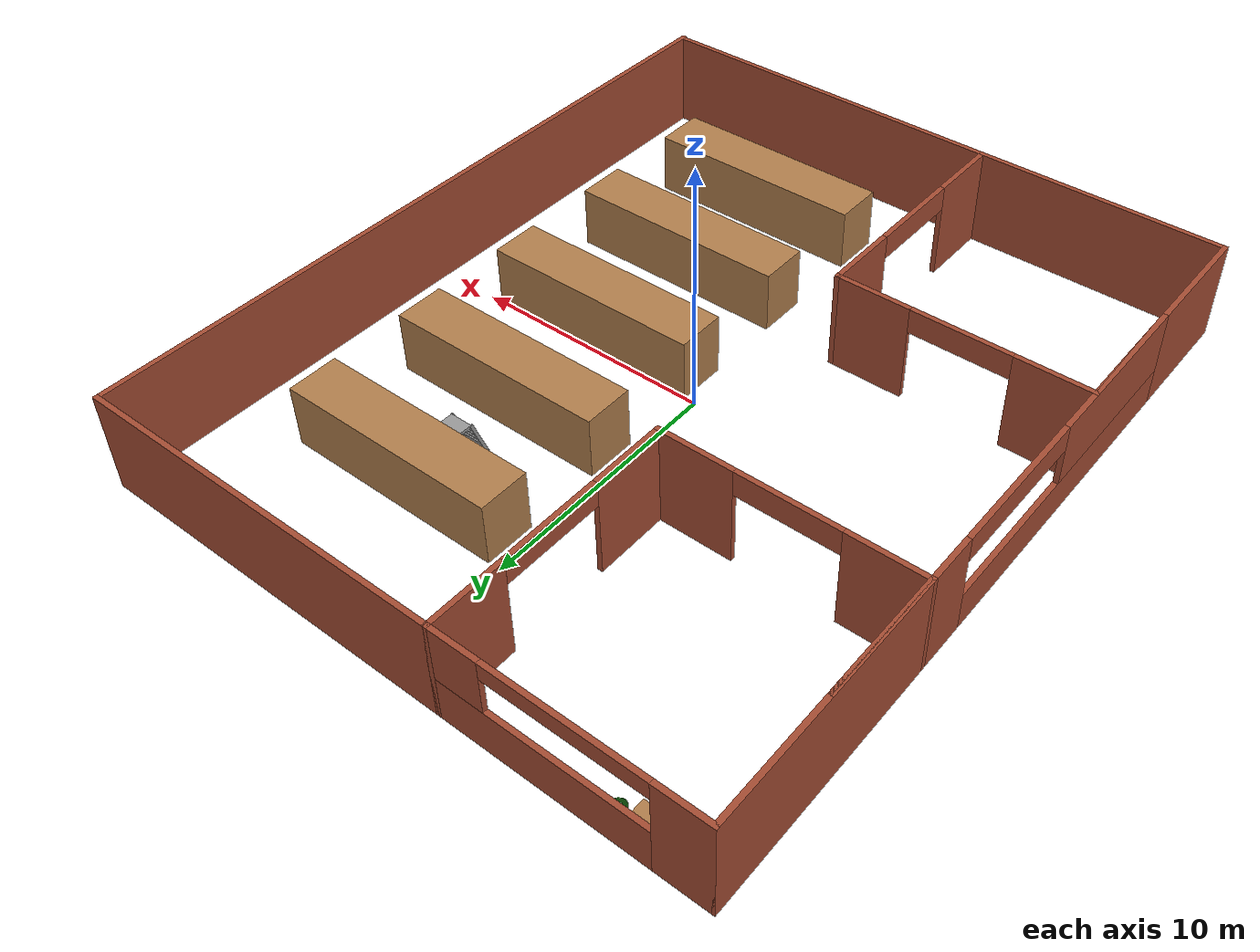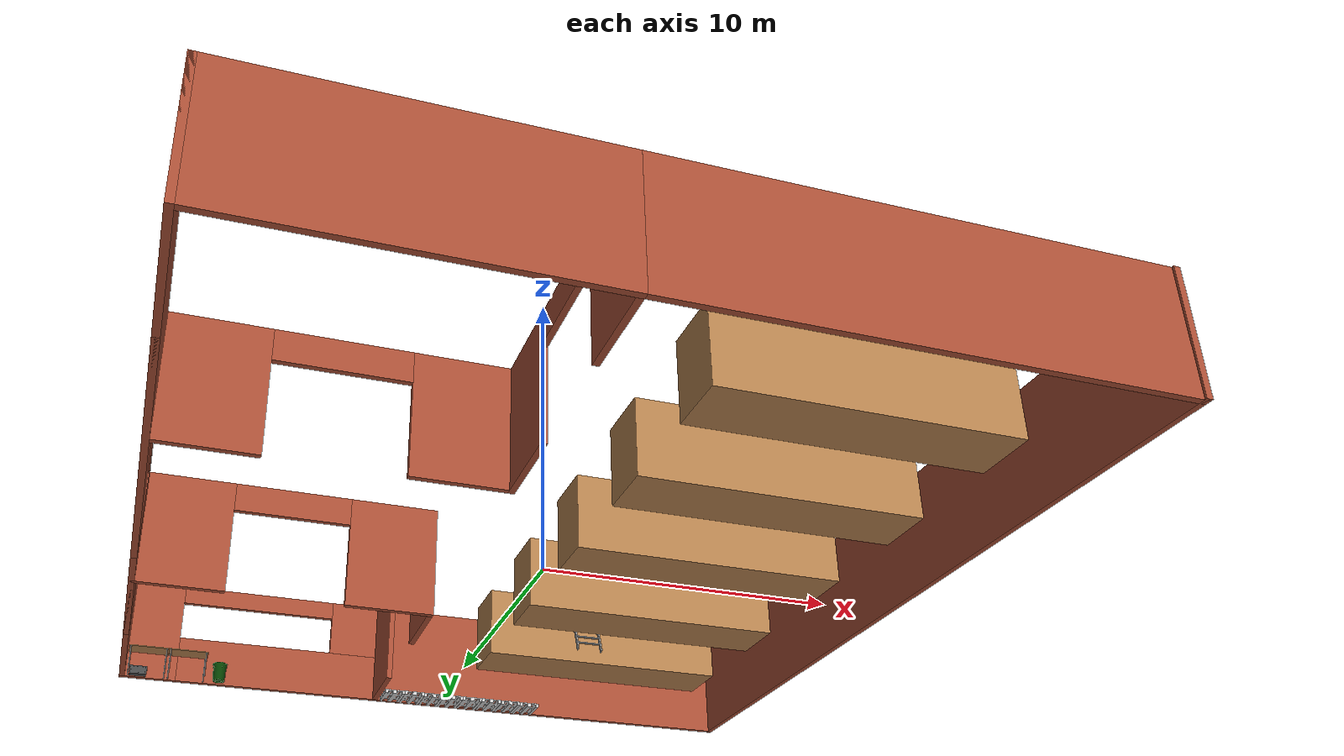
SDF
<?xml version='1.0'?>
<sdf version='1.6'>
  <model name='MyWareHouse'>
    <link name='Wall_12'>
      <pose frame=''>-7.5 -4.9665 0 0 -0 3.14159</pose>
      <self_collide>0</self_collide>
      <enable_wind>0</enable_wind>
      <kinematic>0</kinematic>
      <visual name='Wall_12_Visual_0'>
        <pose frame=''>-3.55 0 2 0 -0 0</pose>
        <geometry>
          <box>
            <size>3.1 0.2 4</size>
          </box>
        </geometry>
        <material>
          <script>
            <uri>file://media/materials/scripts/gazebo.material</uri>
            <name>Gazebo/Bricks</name>
          </script>
          <ambient>1 1 1 1</ambient>
          <shader type='pixel'/>
        </material>
        <meta>
          <layer>0</layer>
        </meta>
        <transparency>0</transparency>
        <cast_shadows>1</cast_shadows>
      </visual>
      <visual name='Wall_12_Visual_1'>
        <pose frame=''>3.55 0 2 0 -0 0</pose>
        <geometry>
          <box>
            <size>3.1 0.2 4</size>
          </box>
        </geometry>
        <material>
          <script>
            <uri>file://media/materials/scripts/gazebo.material</uri>
            <name>Gazebo/Bricks</name>
          </script>
          <ambient>1 1 1 1</ambient>
          <shader type='pixel'/>
        </material>
        <meta>
          <layer>0</layer>
        </meta>
        <transparency>0</transparency>
        <cast_shadows>1</cast_shadows>
      </visual>
      <visual name='Wall_12_Visual_2'>
        <pose frame=''>0 0 3.5 0 -0 0</pose>
        <geometry>
          <box>
            <size>4 0.2 1</size>
          </box>
        </geometry>
        <material>
          <script>
            <uri>file://media/materials/scripts/gazebo.material</uri>
            <name>Gazebo/Bricks</name>
          </script>
          <ambient>1 1 1 1</ambient>
          <shader type='pixel'/>
        </material>
        <meta>
          <layer>0</layer>
        </meta>
        <transparency>0</transparency>
        <cast_shadows>1</cast_shadows>
      </visual>
      <collision name='Wall_12_Collision_0'>
        <laser_retro>0</laser_retro>
        <max_contacts>10</max_contacts>
        <pose frame=''>-3.55 0 2 0 -0 0</pose>
        <geometry>
          <box>
            <size>3.1 0.2 4</size>
          </box>
        </geometry>
        <surface>
          <friction>
            <ode>
              <mu>1</mu>
              <mu2>1</mu2>
              <fdir1>0 0 0</fdir1>
              <slip1>0</slip1>
              <slip2>0</slip2>
            </ode>
            <torsional>
              <coefficient>1</coefficient>
              <patch_radius>0</patch_radius>
              <surface_radius>0</surface_radius>
              <use_patch_radius>1</use_patch_radius>
              <ode>
                <slip>0</slip>
              </ode>
            </torsional>
          </friction>
          <bounce>
            <restitution_coefficient>0</restitution_coefficient>
            <threshold>1e+06</threshold>
          </bounce>
          <contact>
            <collide_without_contact>0</collide_without_contact>
            <collide_without_contact_bitmask>1</collide_without_contact_bitmask>
            <collide_bitmask>1</collide_bitmask>
            <ode>
              <soft_cfm>0</soft_cfm>
              <soft_erp>0.2</soft_erp>
              <kp>1e+13</kp>
              <kd>1</kd>
              <max_vel>0.01</max_vel>
              <min_depth>0</min_depth>
            </ode>
            <bullet>
              <split_impulse>1</split_impulse>
              <split_impulse_penetration_threshold>-0.01</split_impulse_penetration_threshold>
              <soft_cfm>0</soft_cfm>
              <soft_erp>0.2</soft_erp>
              <kp>1e+13</kp>
              <kd>1</kd>
            </bullet>
          </contact>
        </surface>
      </collision>
      <collision name='Wall_12_Collision_1'>
        <laser_retro>0</laser_retro>
        <max_contacts>10</max_contacts>
        <pose frame=''>3.55 0 2 0 -0 0</pose>
        <geometry>
          <box>
            <size>3.1 0.2 4</size>
          </box>
        </geometry>
        <surface>
          <friction>
            <ode>
              <mu>1</mu>
              <mu2>1</mu2>
              <fdir1>0 0 0</fdir1>
              <slip1>0</slip1>
              <slip2>0</slip2>
            </ode>
            <torsional>
              <coefficient>1</coefficient>
              <patch_radius>0</patch_radius>
              <surface_radius>0</surface_radius>
              <use_patch_radius>1</use_patch_radius>
              <ode>
                <slip>0</slip>
              </ode>
            </torsional>
          </friction>
          <bounce>
            <restitution_coefficient>0</restitution_coefficient>
            <threshold>1e+06</threshold>
          </bounce>
          <contact>
            <collide_without_contact>0</collide_without_contact>
            <collide_without_contact_bitmask>1</collide_without_contact_bitmask>
            <collide_bitmask>1</collide_bitmask>
            <ode>
              <soft_cfm>0</soft_cfm>
              <soft_erp>0.2</soft_erp>
              <kp>1e+13</kp>
              <kd>1</kd>
              <max_vel>0.01</max_vel>
              <min_depth>0</min_depth>
            </ode>
            <bullet>
              <split_impulse>1</split_impulse>
              <split_impulse_penetration_threshold>-0.01</split_impulse_penetration_threshold>
              <soft_cfm>0</soft_cfm>
              <soft_erp>0.2</soft_erp>
              <kp>1e+13</kp>
              <kd>1</kd>
            </bullet>
          </contact>
        </surface>
      </collision>
      <collision name='Wall_12_Collision_2'>
        <laser_retro>0</laser_retro>
        <max_contacts>10</max_contacts>
        <pose frame=''>0 0 3.5 0 -0 0</pose>
        <geometry>
          <box>
            <size>4 0.2 1</size>
          </box>
        </geometry>
        <surface>
          <friction>
            <ode>
              <mu>1</mu>
              <mu2>1</mu2>
              <fdir1>0 0 0</fdir1>
              <slip1>0</slip1>
              <slip2>0</slip2>
            </ode>
            <torsional>
              <coefficient>1</coefficient>
              <patch_radius>0</patch_radius>
              <surface_radius>0</surface_radius>
              <use_patch_radius>1</use_patch_radius>
              <ode>
                <slip>0</slip>
              </ode>
            </torsional>
          </friction>
          <bounce>
            <restitution_coefficient>0</restitution_coefficient>
            <threshold>1e+06</threshold>
          </bounce>
          <contact>
            <collide_without_contact>0</collide_without_contact>
            <collide_without_contact_bitmask>1</collide_without_contact_bitmask>
            <collide_bitmask>1</collide_bitmask>
            <ode>
              <soft_cfm>0</soft_cfm>
              <soft_erp>0.2</soft_erp>
              <kp>1e+13</kp>
              <kd>1</kd>
              <max_vel>0.01</max_vel>
              <min_depth>0</min_depth>
            </ode>
            <bullet>
              <split_impulse>1</split_impulse>
              <split_impulse_penetration_threshold>-0.01</split_impulse_penetration_threshold>
              <soft_cfm>0</soft_cfm>
              <soft_erp>0.2</soft_erp>
              <kp>1e+13</kp>
              <kd>1</kd>
            </bullet>
          </contact>
        </surface>
      </collision>
    </link>
    <link name='Wall_13'>
      <pose frame=''>-12.5 -9.9665 0 0 0 -1.5708</pose>
      <self_collide>0</self_collide>
      <enable_wind>0</enable_wind>
      <kinematic>0</kinematic>
      <visual name='Wall_13_Visual'>
        <pose frame=''>0 0 2 0 -0 0</pose>
        <geometry>
          <box>
            <size>10.2 0.2 4</size>
          </box>
        </geometry>
        <material>
          <script>
            <uri>file://media/materials/scripts/gazebo.material</uri>
            <name>Gazebo/Bricks</name>
          </script>
          <ambient>1 1 1 1</ambient>
          <shader type='pixel'/>
        </material>
        <meta>
          <layer>0</layer>
        </meta>
        <transparency>0</transparency>
        <cast_shadows>1</cast_shadows>
      </visual>
      <collision name='Wall_13_Collision'>
        <laser_retro>0</laser_retro>
        <max_contacts>10</max_contacts>
        <pose frame=''>0 0 2 0 -0 0</pose>
        <geometry>
          <box>
            <size>10.2 0.2 4</size>
          </box>
        </geometry>
        <surface>
          <friction>
            <ode>
              <mu>1</mu>
              <mu2>1</mu2>
              <fdir1>0 0 0</fdir1>
              <slip1>0</slip1>
              <slip2>0</slip2>
            </ode>
            <torsional>
              <coefficient>1</coefficient>
              <patch_radius>0</patch_radius>
              <surface_radius>0</surface_radius>
              <use_patch_radius>1</use_patch_radius>
              <ode>
                <slip>0</slip>
              </ode>
            </torsional>
          </friction>
          <bounce>
            <restitution_coefficient>0</restitution_coefficient>
            <threshold>1e+06</threshold>
          </bounce>
          <contact>
            <collide_without_contact>0</collide_without_contact>
            <collide_without_contact_bitmask>1</collide_without_contact_bitmask>
            <collide_bitmask>1</collide_bitmask>
            <ode>
              <soft_cfm>0</soft_cfm>
              <soft_erp>0.2</soft_erp>
              <kp>1e+13</kp>
              <kd>1</kd>
              <max_vel>0.01</max_vel>
              <min_depth>0</min_depth>
            </ode>
            <bullet>
              <split_impulse>1</split_impulse>
              <split_impulse_penetration_threshold>-0.01</split_impulse_penetration_threshold>
              <soft_cfm>0</soft_cfm>
              <soft_erp>0.2</soft_erp>
              <kp>1e+13</kp>
              <kd>1</kd>
            </bullet>
          </contact>
        </surface>
      </collision>
    </link>
    <link name='Wall_14'>
      <pose frame=''>-7.5 -14.9665 0 0 -0 0</pose>
      <self_collide>0</self_collide>
      <enable_wind>0</enable_wind>
      <kinematic>0</kinematic>
      <visual name='Wall_14_Visual'>
        <pose frame=''>0 0 2 0 -0 0</pose>
        <geometry>
          <box>
            <size>10.2 0.2 4</size>
          </box>
        </geometry>
        <material>
          <script>
            <uri>file://media/materials/scripts/gazebo.material</uri>
            <name>Gazebo/Bricks</name>
          </script>
          <ambient>1 1 1 1</ambient>
          <shader type='pixel'/>
        </material>
        <meta>
          <layer>0</layer>
        </meta>
        <transparency>0</transparency>
        <cast_shadows>1</cast_shadows>
      </visual>
      <collision name='Wall_14_Collision'>
        <laser_retro>0</laser_retro>
        <max_contacts>10</max_contacts>
        <pose frame=''>0 0 2 0 -0 0</pose>
        <geometry>
          <box>
            <size>10.2 0.2 4</size>
          </box>
        </geometry>
        <surface>
          <friction>
            <ode>
              <mu>1</mu>
              <mu2>1</mu2>
              <fdir1>0 0 0</fdir1>
              <slip1>0</slip1>
              <slip2>0</slip2>
            </ode>
            <torsional>
              <coefficient>1</coefficient>
              <patch_radius>0</patch_radius>
              <surface_radius>0</surface_radius>
              <use_patch_radius>1</use_patch_radius>
              <ode>
                <slip>0</slip>
              </ode>
            </torsional>
          </friction>
          <bounce>
            <restitution_coefficient>0</restitution_coefficient>
            <threshold>1e+06</threshold>
          </bounce>
          <contact>
            <collide_without_contact>0</collide_without_contact>
            <collide_without_contact_bitmask>1</collide_without_contact_bitmask>
            <collide_bitmask>1</collide_bitmask>
            <ode>
              <soft_cfm>0</soft_cfm>
              <soft_erp>0.2</soft_erp>
              <kp>1e+13</kp>
              <kd>1</kd>
              <max_vel>0.01</max_vel>
              <min_depth>0</min_depth>
            </ode>
            <bullet>
              <split_impulse>1</split_impulse>
              <split_impulse_penetration_threshold>-0.01</split_impulse_penetration_threshold>
              <soft_cfm>0</soft_cfm>
              <soft_erp>0.2</soft_erp>
              <kp>1e+13</kp>
              <kd>1</kd>
            </bullet>
          </contact>
        </surface>
      </collision>
    </link>
    <link name='Wall_15'>
      <pose frame=''>-2.5 -9.9665 0 0 -0 1.5708</pose>
      <self_collide>0</self_collide>
      <enable_wind>0</enable_wind>
      <kinematic>0</kinematic>
      <visual name='Wall_15_Visual_1'>
        <pose frame=''>3.55 0 2 0 -0 0</pose>
        <geometry>
          <box>
            <size>3.1 0.2 4</size>
          </box>
        </geometry>
        <material>
          <script>
            <uri>file://media/materials/scripts/gazebo.material</uri>
            <name>Gazebo/Bricks</name>
          </script>
          <ambient>1 1 1 1</ambient>
          <shader type='pixel'/>
        </material>
        <meta>
          <layer>0</layer>
        </meta>
        <transparency>0</transparency>
        <cast_shadows>1</cast_shadows>
      </visual>
      <visual name='Wall_15_Visual_0'>
        <pose frame=''>-3.55 0 2 0 -0 0</pose>
        <geometry>
          <box>
            <size>3.1 0.2 4</size>
          </box>
        </geometry>
        <material>
          <script>
            <uri>file://media/materials/scripts/gazebo.material</uri>
            <name>Gazebo/Bricks</name>
          </script>
          <ambient>1 1 1 1</ambient>
          <shader type='pixel'/>
        </material>
        <meta>
          <layer>0</layer>
        </meta>
        <transparency>0</transparency>
        <cast_shadows>1</cast_shadows>
      </visual>
      <visual name='Wall_15_Visual_2'>
        <pose frame=''>0 0 3.5 0 -0 0</pose>
        <geometry>
          <box>
            <size>4 0.2 1</size>
          </box>
        </geometry>
        <material>
          <script>
            <uri>file://media/materials/scripts/gazebo.material</uri>
            <name>Gazebo/Bricks</name>
          </script>
          <ambient>1 1 1 1</ambient>
          <shader type='pixel'/>
        </material>
        <meta>
          <layer>0</layer>
        </meta>
        <transparency>0</transparency>
        <cast_shadows>1</cast_shadows>
      </visual>
      <collision name='Wall_15_Collision_0'>
        <laser_retro>0</laser_retro>
        <max_contacts>10</max_contacts>
        <pose frame=''>-3.55 0 2 0 -0 0</pose>
        <geometry>
          <box>
            <size>3.1 0.2 4</size>
          </box>
        </geometry>
        <surface>
          <friction>
            <ode>
              <mu>1</mu>
              <mu2>1</mu2>
              <fdir1>0 0 0</fdir1>
              <slip1>0</slip1>
              <slip2>0</slip2>
            </ode>
            <torsional>
              <coefficient>1</coefficient>
              <patch_radius>0</patch_radius>
              <surface_radius>0</surface_radius>
              <use_patch_radius>1</use_patch_radius>
              <ode>
                <slip>0</slip>
              </ode>
            </torsional>
          </friction>
          <bounce>
            <restitution_coefficient>0</restitution_coefficient>
            <threshold>1e+06</threshold>
          </bounce>
          <contact>
            <collide_without_contact>0</collide_without_contact>
            <collide_without_contact_bitmask>1</collide_without_contact_bitmask>
            <collide_bitmask>1</collide_bitmask>
            <ode>
              <soft_cfm>0</soft_cfm>
              <soft_erp>0.2</soft_erp>
              <kp>1e+13</kp>
              <kd>1</kd>
              <max_vel>0.01</max_vel>
              <min_depth>0</min_depth>
            </ode>
            <bullet>
              <split_impulse>1</split_impulse>
              <split_impulse_penetration_threshold>-0.01</split_impulse_penetration_threshold>
              <soft_cfm>0</soft_cfm>
              <soft_erp>0.2</soft_erp>
              <kp>1e+13</kp>
              <kd>1</kd>
            </bullet>
          </contact>
        </surface>
      </collision>
      <collision name='Wall_15_Collision_1'>
        <laser_retro>0</laser_retro>
        <max_contacts>10</max_contacts>
        <pose frame=''>3.55 0 2 0 -0 0</pose>
        <geometry>
          <box>
            <size>3.1 0.2 4</size>
          </box>
        </geometry>
        <surface>
          <friction>
            <ode>
              <mu>1</mu>
              <mu2>1</mu2>
              <fdir1>0 0 0</fdir1>
              <slip1>0</slip1>
              <slip2>0</slip2>
            </ode>
            <torsional>
              <coefficient>1</coefficient>
              <patch_radius>0</patch_radius>
              <surface_radius>0</surface_radius>
              <use_patch_radius>1</use_patch_radius>
              <ode>
                <slip>0</slip>
              </ode>
            </torsional>
          </friction>
          <bounce>
            <restitution_coefficient>0</restitution_coefficient>
            <threshold>1e+06</threshold>
          </bounce>
          <contact>
            <collide_without_contact>0</collide_without_contact>
            <collide_without_contact_bitmask>1</collide_without_contact_bitmask>
            <collide_bitmask>1</collide_bitmask>
            <ode>
              <soft_cfm>0</soft_cfm>
              <soft_erp>0.2</soft_erp>
              <kp>1e+13</kp>
              <kd>1</kd>
              <max_vel>0.01</max_vel>
              <min_depth>0</min_depth>
            </ode>
            <bullet>
              <split_impulse>1</split_impulse>
              <split_impulse_penetration_threshold>-0.01</split_impulse_penetration_threshold>
              <soft_cfm>0</soft_cfm>
              <soft_erp>0.2</soft_erp>
              <kp>1e+13</kp>
              <kd>1</kd>
            </bullet>
          </contact>
        </surface>
      </collision>
      <collision name='Wall_15_Collision_2'>
        <laser_retro>0</laser_retro>
        <max_contacts>10</max_contacts>
        <pose frame=''>0 0 3.5 0 -0 0</pose>
        <geometry>
          <box>
            <size>4 0.2 1</size>
          </box>
        </geometry>
        <surface>
          <friction>
            <ode>
              <mu>1</mu>
              <mu2>1</mu2>
              <fdir1>0 0 0</fdir1>
              <slip1>0</slip1>
              <slip2>0</slip2>
            </ode>
            <torsional>
              <coefficient>1</coefficient>
              <patch_radius>0</patch_radius>
              <surface_radius>0</surface_radius>
              <use_patch_radius>1</use_patch_radius>
              <ode>
                <slip>0</slip>
              </ode>
            </torsional>
          </friction>
          <bounce>
            <restitution_coefficient>0</restitution_coefficient>
            <threshold>1e+06</threshold>
          </bounce>
          <contact>
            <collide_without_contact>0</collide_without_contact>
            <collide_without_contact_bitmask>1</collide_without_contact_bitmask>
            <collide_bitmask>1</collide_bitmask>
            <ode>
              <soft_cfm>0</soft_cfm>
              <soft_erp>0.2</soft_erp>
              <kp>1e+13</kp>
              <kd>1</kd>
              <max_vel>0.01</max_vel>
              <min_depth>0</min_depth>
            </ode>
            <bullet>
              <split_impulse>1</split_impulse>
              <split_impulse_penetration_threshold>-0.01</split_impulse_penetration_threshold>
              <soft_cfm>0</soft_cfm>
              <soft_erp>0.2</soft_erp>
              <kp>1e+13</kp>
              <kd>1</kd>
            </bullet>
          </contact>
        </surface>
      </collision>
    </link>
    <link name='Wall_17'>
      <pose frame=''>-12.5 0.033501 0 0 0 -1.5708</pose>
      <self_collide>0</self_collide>
      <enable_wind>0</enable_wind>
      <kinematic>0</kinematic>
      <visual name='Wall_17_Visual_0'>
        <pose frame=''>-6.55 0 2 0 -0 0</pose>
        <geometry>
          <box>
            <size>7.1 0.2 4</size>
          </box>
        </geometry>
        <material>
          <script>
            <uri>file://media/materials/scripts/gazebo.material</uri>
            <name>Gazebo/Bricks</name>
          </script>
          <ambient>1 1 1 1</ambient>
          <shader type='pixel'/>
        </material>
        <meta>
          <layer>0</layer>
        </meta>
        <transparency>0</transparency>
        <cast_shadows>1</cast_shadows>
      </visual>
      <visual name='Wall_17_Visual_1'>
        <pose frame=''>3.55 0 0.75 0 -0 0</pose>
        <geometry>
          <box>
            <size>13.1 0.2 1.5</size>
          </box>
        </geometry>
        <material>
          <script>
            <uri>file://media/materials/scripts/gazebo.material</uri>
            <name>Gazebo/Bricks</name>
          </script>
          <ambient>1 1 1 1</ambient>
          <shader type='pixel'/>
        </material>
        <meta>
          <layer>0</layer>
        </meta>
        <transparency>0</transparency>
        <cast_shadows>1</cast_shadows>
      </visual>
      <visual name='Wall_17_Visual_2'>
        <pose frame=''>6.55 0 2.75 0 -0 0</pose>
        <geometry>
          <box>
            <size>7.1 0.2 2.5</size>
          </box>
        </geometry>
        <material>
          <script>
            <uri>file://media/materials/scripts/gazebo.material</uri>
            <name>Gazebo/Bricks</name>
          </script>
          <ambient>1 1 1 1</ambient>
          <shader type='pixel'/>
        </material>
        <meta>
          <layer>0</layer>
        </meta>
        <transparency>0</transparency>
        <cast_shadows>1</cast_shadows>
      </visual>
      <visual name='Wall_17_Visual_3'>
        <pose frame=''>0 0 3.5 0 -0 0</pose>
        <geometry>
          <box>
            <size>6 0.2 1</size>
          </box>
        </geometry>
        <material>
          <script>
            <uri>file://media/materials/scripts/gazebo.material</uri>
            <name>Gazebo/Bricks</name>
          </script>
          <ambient>1 1 1 1</ambient>
          <shader type='pixel'/>
        </material>
        <meta>
          <layer>0</layer>
        </meta>
        <transparency>0</transparency>
        <cast_shadows>1</cast_shadows>
      </visual>
      <collision name='Wall_17_Collision_2'>
        <laser_retro>0</laser_retro>
        <max_contacts>10</max_contacts>
        <pose frame=''>6.55 0 2.75 0 -0 0</pose>
        <geometry>
          <box>
            <size>7.1 0.2 2.5</size>
          </box>
        </geometry>
        <surface>
          <friction>
            <ode>
              <mu>1</mu>
              <mu2>1</mu2>
              <fdir1>0 0 0</fdir1>
              <slip1>0</slip1>
              <slip2>0</slip2>
            </ode>
            <torsional>
              <coefficient>1</coefficient>
              <patch_radius>0</patch_radius>
              <surface_radius>0</surface_radius>
              <use_patch_radius>1</use_patch_radius>
              <ode>
                <slip>0</slip>
              </ode>
            </torsional>
          </friction>
          <bounce>
            <restitution_coefficient>0</restitution_coefficient>
            <threshold>1e+06</threshold>
          </bounce>
          <contact>
            <collide_without_contact>0</collide_without_contact>
            <collide_without_contact_bitmask>1</collide_without_contact_bitmask>
            <collide_bitmask>1</collide_bitmask>
            <ode>
              <soft_cfm>0</soft_cfm>
              <soft_erp>0.2</soft_erp>
              <kp>1e+13</kp>
              <kd>1</kd>
              <max_vel>0.01</max_vel>
              <min_depth>0</min_depth>
            </ode>
            <bullet>
              <split_impulse>1</split_impulse>
              <split_impulse_penetration_threshold>-0.01</split_impulse_penetration_threshold>
              <soft_cfm>0</soft_cfm>
              <soft_erp>0.2</soft_erp>
              <kp>1e+13</kp>
              <kd>1</kd>
            </bullet>
          </contact>
        </surface>
      </collision>
      <collision name='Wall_17_Collision_0'>
        <laser_retro>0</laser_retro>
        <max_contacts>10</max_contacts>
        <pose frame=''>-6.55 0 2 0 -0 0</pose>
        <geometry>
          <box>
            <size>7.1 0.2 4</size>
          </box>
        </geometry>
        <surface>
          <friction>
            <ode>
              <mu>1</mu>
              <mu2>1</mu2>
              <fdir1>0 0 0</fdir1>
              <slip1>0</slip1>
              <slip2>0</slip2>
            </ode>
            <torsional>
              <coefficient>1</coefficient>
              <patch_radius>0</patch_radius>
              <surface_radius>0</surface_radius>
              <use_patch_radius>1</use_patch_radius>
              <ode>
                <slip>0</slip>
              </ode>
            </torsional>
          </friction>
          <bounce>
            <restitution_coefficient>0</restitution_coefficient>
            <threshold>1e+06</threshold>
          </bounce>
          <contact>
            <collide_without_contact>0</collide_without_contact>
            <collide_without_contact_bitmask>1</collide_without_contact_bitmask>
            <collide_bitmask>1</collide_bitmask>
            <ode>
              <soft_cfm>0</soft_cfm>
              <soft_erp>0.2</soft_erp>
              <kp>1e+13</kp>
              <kd>1</kd>
              <max_vel>0.01</max_vel>
              <min_depth>0</min_depth>
            </ode>
            <bullet>
              <split_impulse>1</split_impulse>
              <split_impulse_penetration_threshold>-0.01</split_impulse_penetration_threshold>
              <soft_cfm>0</soft_cfm>
              <soft_erp>0.2</soft_erp>
              <kp>1e+13</kp>
              <kd>1</kd>
            </bullet>
          </contact>
        </surface>
      </collision>
      <collision name='Wall_17_Collision_1'>
        <laser_retro>0</laser_retro>
        <max_contacts>10</max_contacts>
        <pose frame=''>3.55 0 0.75 0 -0 0</pose>
        <geometry>
          <box>
            <size>13.1 0.2 1.5</size>
          </box>
        </geometry>
        <surface>
          <friction>
            <ode>
              <mu>1</mu>
              <mu2>1</mu2>
              <fdir1>0 0 0</fdir1>
              <slip1>0</slip1>
              <slip2>0</slip2>
            </ode>
            <torsional>
              <coefficient>1</coefficient>
              <patch_radius>0</patch_radius>
              <surface_radius>0</surface_radius>
              <use_patch_radius>1</use_patch_radius>
              <ode>
                <slip>0</slip>
              </ode>
            </torsional>
          </friction>
          <bounce>
            <restitution_coefficient>0</restitution_coefficient>
            <threshold>1e+06</threshold>
          </bounce>
          <contact>
            <collide_without_contact>0</collide_without_contact>
            <collide_without_contact_bitmask>1</collide_without_contact_bitmask>
            <collide_bitmask>1</collide_bitmask>
            <ode>
              <soft_cfm>0</soft_cfm>
              <soft_erp>0.2</soft_erp>
              <kp>1e+13</kp>
              <kd>1</kd>
              <max_vel>0.01</max_vel>
              <min_depth>0</min_depth>
            </ode>
            <bullet>
              <split_impulse>1</split_impulse>
              <split_impulse_penetration_threshold>-0.01</split_impulse_penetration_threshold>
              <soft_cfm>0</soft_cfm>
              <soft_erp>0.2</soft_erp>
              <kp>1e+13</kp>
              <kd>1</kd>
            </bullet>
          </contact>
        </surface>
      </collision>
      <collision name='Wall_17_Collision_3'>
        <laser_retro>0</laser_retro>
        <max_contacts>10</max_contacts>
        <pose frame=''>0 0 3.5 0 -0 0</pose>
        <geometry>
          <box>
            <size>6 0.2 1</size>
          </box>
        </geometry>
        <surface>
          <friction>
            <ode>
              <mu>1</mu>
              <mu2>1</mu2>
              <fdir1>0 0 0</fdir1>
              <slip1>0</slip1>
              <slip2>0</slip2>
            </ode>
            <torsional>
              <coefficient>1</coefficient>
              <patch_radius>0</patch_radius>
              <surface_radius>0</surface_radius>
              <use_patch_radius>1</use_patch_radius>
              <ode>
                <slip>0</slip>
              </ode>
            </torsional>
          </friction>
          <bounce>
            <restitution_coefficient>0</restitution_coefficient>
            <threshold>1e+06</threshold>
          </bounce>
          <contact>
            <collide_without_contact>0</collide_without_contact>
            <collide_without_contact_bitmask>1</collide_without_contact_bitmask>
            <collide_bitmask>1</collide_bitmask>
            <ode>
              <soft_cfm>0</soft_cfm>
              <soft_erp>0.2</soft_erp>
              <kp>1e+13</kp>
              <kd>1</kd>
              <max_vel>0.01</max_vel>
              <min_depth>0</min_depth>
            </ode>
            <bullet>
              <split_impulse>1</split_impulse>
              <split_impulse_penetration_threshold>-0.01</split_impulse_penetration_threshold>
              <soft_cfm>0</soft_cfm>
              <soft_erp>0.2</soft_erp>
              <kp>1e+13</kp>
              <kd>1</kd>
            </bullet>
          </contact>
        </surface>
      </collision>
    </link>
    <link name='Wall_19'>
      <pose frame=''>5 15.0335 0 0 -0 0</pose>
      <self_collide>0</self_collide>
      <enable_wind>0</enable_wind>
      <kinematic>0</kinematic>
      <visual name='Wall_19_Visual'>
        <pose frame=''>0 0 2 0 -0 0</pose>
        <geometry>
          <box>
            <size>15.2 0.2 4</size>
          </box>
        </geometry>
        <material>
          <script>
            <uri>file://media/materials/scripts/gazebo.material</uri>
            <name>Gazebo/Bricks</name>
          </script>
          <ambient>1 1 1 1</ambient>
          <shader type='pixel'/>
        </material>
        <meta>
          <layer>0</layer>
        </meta>
        <transparency>0</transparency>
        <cast_shadows>1</cast_shadows>
      </visual>
      <collision name='Wall_19_Collision'>
        <laser_retro>0</laser_retro>
        <max_contacts>10</max_contacts>
        <pose frame=''>0 0 2 0 -0 0</pose>
        <geometry>
          <box>
            <size>15.2 0.2 4</size>
          </box>
        </geometry>
        <surface>
          <friction>
            <ode>
              <mu>1</mu>
              <mu2>1</mu2>
              <fdir1>0 0 0</fdir1>
              <slip1>0</slip1>
              <slip2>0</slip2>
            </ode>
            <torsional>
              <coefficient>1</coefficient>
              <patch_radius>0</patch_radius>
              <surface_radius>0</surface_radius>
              <use_patch_radius>1</use_patch_radius>
              <ode>
                <slip>0</slip>
              </ode>
            </torsional>
          </friction>
          <bounce>
            <restitution_coefficient>0</restitution_coefficient>
            <threshold>1e+06</threshold>
          </bounce>
          <contact>
            <collide_without_contact>0</collide_without_contact>
            <collide_without_contact_bitmask>1</collide_without_contact_bitmask>
            <collide_bitmask>1</collide_bitmask>
            <ode>
              <soft_cfm>0</soft_cfm>
              <soft_erp>0.2</soft_erp>
              <kp>1e+13</kp>
              <kd>1</kd>
              <max_vel>0.01</max_vel>
              <min_depth>0</min_depth>
            </ode>
            <bullet>
              <split_impulse>1</split_impulse>
              <split_impulse_penetration_threshold>-0.01</split_impulse_penetration_threshold>
              <soft_cfm>0</soft_cfm>
              <soft_erp>0.2</soft_erp>
              <kp>1e+13</kp>
              <kd>1</kd>
            </bullet>
          </contact>
        </surface>
      </collision>
    </link>
    <link name='Wall_2'>
      <pose frame=''>-7.5 15.0335 0 0 -0 0</pose>
      <self_collide>0</self_collide>
      <enable_wind>0</enable_wind>
      <kinematic>0</kinematic>
      <visual name='Wall_2_Visual_0'>
        <pose frame=''>-4.04112 0 2 0 -0 0</pose>
        <geometry>
          <box>
            <size>2.11776 0.2 4</size>
          </box>
        </geometry>
        <material>
          <script>
            <uri>file://media/materials/scripts/gazebo.material</uri>
            <name>Gazebo/Bricks</name>
          </script>
          <ambient>1 1 1 1</ambient>
          <shader type='pixel'/>
        </material>
        <meta>
          <layer>0</layer>
        </meta>
        <transparency>0</transparency>
        <cast_shadows>1</cast_shadows>
      </visual>
      <visual name='Wall_2_Visual_1'>
        <pose frame=''>1.05888 0 0.9 0 -0 0</pose>
        <geometry>
          <box>
            <size>8.08224 0.2 1.8</size>
          </box>
        </geometry>
        <material>
          <script>
            <uri>file://media/materials/scripts/gazebo.material</uri>
            <name>Gazebo/Bricks</name>
          </script>
          <ambient>1 1 1 1</ambient>
          <shader type='pixel'/>
        </material>
        <meta>
          <layer>0</layer>
        </meta>
        <transparency>0</transparency>
        <cast_shadows>1</cast_shadows>
      </visual>
      <visual name='Wall_2_Visual_2'>
        <pose frame=''>4.05888 0 2.9 0 -0 0</pose>
        <geometry>
          <box>
            <size>2.08224 0.2 2.2</size>
          </box>
        </geometry>
        <material>
          <script>
            <uri>file://media/materials/scripts/gazebo.material</uri>
            <name>Gazebo/Bricks</name>
          </script>
          <ambient>1 1 1 1</ambient>
          <shader type='pixel'/>
        </material>
        <meta>
          <layer>0</layer>
        </meta>
        <transparency>0</transparency>
        <cast_shadows>1</cast_shadows>
      </visual>
      <visual name='Wall_2_Visual_3'>
        <pose frame=''>0.01776 0 3.65 0 -0 0</pose>
        <geometry>
          <box>
            <size>6 0.2 0.7</size>
          </box>
        </geometry>
        <material>
          <script>
            <uri>file://media/materials/scripts/gazebo.material</uri>
            <name>Gazebo/Bricks</name>
          </script>
          <ambient>1 1 1 1</ambient>
          <shader type='pixel'/>
        </material>
        <meta>
          <layer>0</layer>
        </meta>
        <transparency>0</transparency>
        <cast_shadows>1</cast_shadows>
      </visual>
      <collision name='Wall_2_Collision_0'>
        <laser_retro>0</laser_retro>
        <max_contacts>10</max_contacts>
        <pose frame=''>-4.04112 0 2 0 -0 0</pose>
        <geometry>
          <box>
            <size>2.11776 0.2 4</size>
          </box>
        </geometry>
        <surface>
          <friction>
            <ode>
              <mu>1</mu>
              <mu2>1</mu2>
              <fdir1>0 0 0</fdir1>
              <slip1>0</slip1>
              <slip2>0</slip2>
            </ode>
            <torsional>
              <coefficient>1</coefficient>
              <patch_radius>0</patch_radius>
              <surface_radius>0</surface_radius>
              <use_patch_radius>1</use_patch_radius>
              <ode>
                <slip>0</slip>
              </ode>
            </torsional>
          </friction>
          <bounce>
            <restitution_coefficient>0</restitution_coefficient>
            <threshold>1e+06</threshold>
          </bounce>
          <contact>
            <collide_without_contact>0</collide_without_contact>
            <collide_without_contact_bitmask>1</collide_without_contact_bitmask>
            <collide_bitmask>1</collide_bitmask>
            <ode>
              <soft_cfm>0</soft_cfm>
              <soft_erp>0.2</soft_erp>
              <kp>1e+13</kp>
              <kd>1</kd>
              <max_vel>0.01</max_vel>
              <min_depth>0</min_depth>
            </ode>
            <bullet>
              <split_impulse>1</split_impulse>
              <split_impulse_penetration_threshold>-0.01</split_impulse_penetration_threshold>
              <soft_cfm>0</soft_cfm>
              <soft_erp>0.2</soft_erp>
              <kp>1e+13</kp>
              <kd>1</kd>
            </bullet>
          </contact>
        </surface>
      </collision>
      <collision name='Wall_2_Collision_1'>
        <laser_retro>0</laser_retro>
        <max_contacts>10</max_contacts>
        <pose frame=''>1.05888 0 0.9 0 -0 0</pose>
        <geometry>
          <box>
            <size>8.08224 0.2 1.8</size>
          </box>
        </geometry>
        <surface>
          <friction>
            <ode>
              <mu>1</mu>
              <mu2>1</mu2>
              <fdir1>0 0 0</fdir1>
              <slip1>0</slip1>
              <slip2>0</slip2>
            </ode>
            <torsional>
              <coefficient>1</coefficient>
              <patch_radius>0</patch_radius>
              <surface_radius>0</surface_radius>
              <use_patch_radius>1</use_patch_radius>
              <ode>
                <slip>0</slip>
              </ode>
            </torsional>
          </friction>
          <bounce>
            <restitution_coefficient>0</restitution_coefficient>
            <threshold>1e+06</threshold>
          </bounce>
          <contact>
            <collide_without_contact>0</collide_without_contact>
            <collide_without_contact_bitmask>1</collide_without_contact_bitmask>
            <collide_bitmask>1</collide_bitmask>
            <ode>
              <soft_cfm>0</soft_cfm>
              <soft_erp>0.2</soft_erp>
              <kp>1e+13</kp>
              <kd>1</kd>
              <max_vel>0.01</max_vel>
              <min_depth>0</min_depth>
            </ode>
            <bullet>
              <split_impulse>1</split_impulse>
              <split_impulse_penetration_threshold>-0.01</split_impulse_penetration_threshold>
              <soft_cfm>0</soft_cfm>
              <soft_erp>0.2</soft_erp>
              <kp>1e+13</kp>
              <kd>1</kd>
            </bullet>
          </contact>
        </surface>
      </collision>
      <collision name='Wall_2_Collision_2'>
        <laser_retro>0</laser_retro>
        <max_contacts>10</max_contacts>
        <pose frame=''>4.05888 0 2.9 0 -0 0</pose>
        <geometry>
          <box>
            <size>2.08224 0.2 2.2</size>
          </box>
        </geometry>
        <surface>
          <friction>
            <ode>
              <mu>1</mu>
              <mu2>1</mu2>
              <fdir1>0 0 0</fdir1>
              <slip1>0</slip1>
              <slip2>0</slip2>
            </ode>
            <torsional>
              <coefficient>1</coefficient>
              <patch_radius>0</patch_radius>
              <surface_radius>0</surface_radius>
              <use_patch_radius>1</use_patch_radius>
              <ode>
                <slip>0</slip>
              </ode>
            </torsional>
          </friction>
          <bounce>
            <restitution_coefficient>0</restitution_coefficient>
            <threshold>1e+06</threshold>
          </bounce>
          <contact>
            <collide_without_contact>0</collide_without_contact>
            <collide_without_contact_bitmask>1</collide_without_contact_bitmask>
            <collide_bitmask>1</collide_bitmask>
            <ode>
              <soft_cfm>0</soft_cfm>
              <soft_erp>0.2</soft_erp>
              <kp>1e+13</kp>
              <kd>1</kd>
              <max_vel>0.01</max_vel>
              <min_depth>0</min_depth>
            </ode>
            <bullet>
              <split_impulse>1</split_impulse>
              <split_impulse_penetration_threshold>-0.01</split_impulse_penetration_threshold>
              <soft_cfm>0</soft_cfm>
              <soft_erp>0.2</soft_erp>
              <kp>1e+13</kp>
              <kd>1</kd>
            </bullet>
          </contact>
        </surface>
      </collision>
      <collision name='Wall_2_Collision_3'>
        <laser_retro>0</laser_retro>
        <max_contacts>10</max_contacts>
        <pose frame=''>0.01776 0 3.65 0 -0 0</pose>
        <geometry>
          <box>
            <size>6 0.2 0.7</size>
          </box>
        </geometry>
        <surface>
          <friction>
            <ode>
              <mu>1</mu>
              <mu2>1</mu2>
              <fdir1>0 0 0</fdir1>
              <slip1>0</slip1>
              <slip2>0</slip2>
            </ode>
            <torsional>
              <coefficient>1</coefficient>
              <patch_radius>0</patch_radius>
              <surface_radius>0</surface_radius>
              <use_patch_radius>1</use_patch_radius>
              <ode>
                <slip>0</slip>
              </ode>
            </torsional>
          </friction>
          <bounce>
            <restitution_coefficient>0</restitution_coefficient>
            <threshold>1e+06</threshold>
          </bounce>
          <contact>
            <collide_without_contact>0</collide_without_contact>
            <collide_without_contact_bitmask>1</collide_without_contact_bitmask>
            <collide_bitmask>1</collide_bitmask>
            <ode>
              <soft_cfm>0</soft_cfm>
              <soft_erp>0.2</soft_erp>
              <kp>1e+13</kp>
              <kd>1</kd>
              <max_vel>0.01</max_vel>
              <min_depth>0</min_depth>
            </ode>
            <bullet>
              <split_impulse>1</split_impulse>
              <split_impulse_penetration_threshold>-0.01</split_impulse_penetration_threshold>
              <soft_cfm>0</soft_cfm>
              <soft_erp>0.2</soft_erp>
              <kp>1e+13</kp>
              <kd>1</kd>
            </bullet>
          </contact>
        </surface>
      </collision>
    </link>
    <link name='Wall_21'>
      <pose frame=''>12.5 -0.033499 0 0 0 -1.5708</pose>
      <self_collide>0</self_collide>
      <enable_wind>0</enable_wind>
      <kinematic>0</kinematic>
      <visual name='Wall_21_Visual'>
        <pose frame=''>0 0 2 0 -0 0</pose>
        <geometry>
          <box>
            <size>30.2 0.2 4</size>
          </box>
        </geometry>
        <material>
          <script>
            <uri>file://media/materials/scripts/gazebo.material</uri>
            <name>Gazebo/Bricks</name>
          </script>
          <ambient>1 1 1 1</ambient>
          <shader type='pixel'/>
        </material>
        <meta>
          <layer>0</layer>
        </meta>
        <transparency>0</transparency>
        <cast_shadows>1</cast_shadows>
      </visual>
      <collision name='Wall_21_Collision'>
        <laser_retro>0</laser_retro>
        <max_contacts>10</max_contacts>
        <pose frame=''>0 0 2 0 -0 0</pose>
        <geometry>
          <box>
            <size>30.2 0.2 4</size>
          </box>
        </geometry>
        <surface>
          <friction>
            <ode>
              <mu>1</mu>
              <mu2>1</mu2>
              <fdir1>0 0 0</fdir1>
              <slip1>0</slip1>
              <slip2>0</slip2>
            </ode>
            <torsional>
              <coefficient>1</coefficient>
              <patch_radius>0</patch_radius>
              <surface_radius>0</surface_radius>
              <use_patch_radius>1</use_patch_radius>
              <ode>
                <slip>0</slip>
              </ode>
            </torsional>
          </friction>
          <bounce>
            <restitution_coefficient>0</restitution_coefficient>
            <threshold>1e+06</threshold>
          </bounce>
          <contact>
            <collide_without_contact>0</collide_without_contact>
            <collide_without_contact_bitmask>1</collide_without_contact_bitmask>
            <collide_bitmask>1</collide_bitmask>
            <ode>
              <soft_cfm>0</soft_cfm>
              <soft_erp>0.2</soft_erp>
              <kp>1e+13</kp>
              <kd>1</kd>
              <max_vel>0.01</max_vel>
              <min_depth>0</min_depth>
            </ode>
            <bullet>
              <split_impulse>1</split_impulse>
              <split_impulse_penetration_threshold>-0.01</split_impulse_penetration_threshold>
              <soft_cfm>0</soft_cfm>
              <soft_erp>0.2</soft_erp>
              <kp>1e+13</kp>
              <kd>1</kd>
            </bullet>
          </contact>
        </surface>
      </collision>
    </link>
    <link name='Wall_23'>
      <pose frame=''>5 -14.9665 0 0 -0 0</pose>
      <self_collide>0</self_collide>
      <enable_wind>0</enable_wind>
      <kinematic>0</kinematic>
      <visual name='Wall_23_Visual'>
        <pose frame=''>0 0 2 0 -0 0</pose>
        <geometry>
          <box>
            <size>15.2 0.2 4</size>
          </box>
        </geometry>
        <material>
          <script>
            <uri>file://media/materials/scripts/gazebo.material</uri>
            <name>Gazebo/Bricks</name>
          </script>
          <ambient>1 1 1 1</ambient>
          <shader type='pixel'/>
        </material>
        <meta>
          <layer>0</layer>
        </meta>
        <transparency>0</transparency>
        <cast_shadows>1</cast_shadows>
      </visual>
      <collision name='Wall_23_Collision'>
        <laser_retro>0</laser_retro>
        <max_contacts>10</max_contacts>
        <pose frame=''>0 0 2 0 -0 0</pose>
        <geometry>
          <box>
            <size>15.2 0.2 4</size>
          </box>
        </geometry>
        <surface>
          <friction>
            <ode>
              <mu>1</mu>
              <mu2>1</mu2>
              <fdir1>0 0 0</fdir1>
              <slip1>0</slip1>
              <slip2>0</slip2>
            </ode>
            <torsional>
              <coefficient>1</coefficient>
              <patch_radius>0</patch_radius>
              <surface_radius>0</surface_radius>
              <use_patch_radius>1</use_patch_radius>
              <ode>
                <slip>0</slip>
              </ode>
            </torsional>
          </friction>
          <bounce>
            <restitution_coefficient>0</restitution_coefficient>
            <threshold>1e+06</threshold>
          </bounce>
          <contact>
            <collide_without_contact>0</collide_without_contact>
            <collide_without_contact_bitmask>1</collide_without_contact_bitmask>
            <collide_bitmask>1</collide_bitmask>
            <ode>
              <soft_cfm>0</soft_cfm>
              <soft_erp>0.2</soft_erp>
              <kp>1e+13</kp>
              <kd>1</kd>
              <max_vel>0.01</max_vel>
              <min_depth>0</min_depth>
            </ode>
            <bullet>
              <split_impulse>1</split_impulse>
              <split_impulse_penetration_threshold>-0.01</split_impulse_penetration_threshold>
              <soft_cfm>0</soft_cfm>
              <soft_erp>0.2</soft_erp>
              <kp>1e+13</kp>
              <kd>1</kd>
            </bullet>
          </contact>
        </surface>
      </collision>
    </link>
    <link name='Wall_4'>
      <pose frame=''>-2.5 10.0335 0 0 0 -1.5708</pose>
      <self_collide>0</self_collide>
      <enable_wind>0</enable_wind>
      <kinematic>0</kinematic>
      <visual name='Wall_4_Visual_0'>
        <pose frame=''>-3.54841 0 2 0 -0 0</pose>
        <geometry>
          <box>
            <size>3.10318 0.2 4</size>
          </box>
        </geometry>
        <material>
          <script>
            <uri>file://media/materials/scripts/gazebo.material</uri>
            <name>Gazebo/Bricks</name>
          </script>
          <ambient>1 1 1 1</ambient>
          <shader type='pixel'/>
        </material>
        <meta>
          <layer>0</layer>
        </meta>
        <transparency>0</transparency>
        <cast_shadows>1</cast_shadows>
      </visual>
      <visual name='Wall_4_Visual_1'>
        <pose frame=''>3.55159 0 2 0 -0 0</pose>
        <geometry>
          <box>
            <size>3.09682 0.2 4</size>
          </box>
        </geometry>
        <material>
          <script>
            <uri>file://media/materials/scripts/gazebo.material</uri>
            <name>Gazebo/Bricks</name>
          </script>
          <ambient>1 1 1 1</ambient>
          <shader type='pixel'/>
        </material>
        <meta>
          <layer>0</layer>
        </meta>
        <transparency>0</transparency>
        <cast_shadows>1</cast_shadows>
      </visual>
      <visual name='Wall_4_Visual_2'>
        <pose frame=''>0.003178 0 3.5 0 -0 0</pose>
        <geometry>
          <box>
            <size>4 0.2 1</size>
          </box>
        </geometry>
        <material>
          <script>
            <uri>file://media/materials/scripts/gazebo.material</uri>
            <name>Gazebo/Bricks</name>
          </script>
          <ambient>1 1 1 1</ambient>
          <shader type='pixel'/>
        </material>
        <meta>
          <layer>0</layer>
        </meta>
        <transparency>0</transparency>
        <cast_shadows>1</cast_shadows>
      </visual>
      <collision name='Wall_4_Collision_0'>
        <laser_retro>0</laser_retro>
        <max_contacts>10</max_contacts>
        <pose frame=''>-3.54841 0 2 0 -0 0</pose>
        <geometry>
          <box>
            <size>3.10318 0.2 4</size>
          </box>
        </geometry>
        <surface>
          <friction>
            <ode>
              <mu>1</mu>
              <mu2>1</mu2>
              <fdir1>0 0 0</fdir1>
              <slip1>0</slip1>
              <slip2>0</slip2>
            </ode>
            <torsional>
              <coefficient>1</coefficient>
              <patch_radius>0</patch_radius>
              <surface_radius>0</surface_radius>
              <use_patch_radius>1</use_patch_radius>
              <ode>
                <slip>0</slip>
              </ode>
            </torsional>
          </friction>
          <bounce>
            <restitution_coefficient>0</restitution_coefficient>
            <threshold>1e+06</threshold>
          </bounce>
          <contact>
            <collide_without_contact>0</collide_without_contact>
            <collide_without_contact_bitmask>1</collide_without_contact_bitmask>
            <collide_bitmask>1</collide_bitmask>
            <ode>
              <soft_cfm>0</soft_cfm>
              <soft_erp>0.2</soft_erp>
              <kp>1e+13</kp>
              <kd>1</kd>
              <max_vel>0.01</max_vel>
              <min_depth>0</min_depth>
            </ode>
            <bullet>
              <split_impulse>1</split_impulse>
              <split_impulse_penetration_threshold>-0.01</split_impulse_penetration_threshold>
              <soft_cfm>0</soft_cfm>
              <soft_erp>0.2</soft_erp>
              <kp>1e+13</kp>
              <kd>1</kd>
            </bullet>
          </contact>
        </surface>
      </collision>
      <collision name='Wall_4_Collision_1'>
        <laser_retro>0</laser_retro>
        <max_contacts>10</max_contacts>
        <pose frame=''>3.55159 0 2 0 -0 0</pose>
        <geometry>
          <box>
            <size>3.09682 0.2 4</size>
          </box>
        </geometry>
        <surface>
          <friction>
            <ode>
              <mu>1</mu>
              <mu2>1</mu2>
              <fdir1>0 0 0</fdir1>
              <slip1>0</slip1>
              <slip2>0</slip2>
            </ode>
            <torsional>
              <coefficient>1</coefficient>
              <patch_radius>0</patch_radius>
              <surface_radius>0</surface_radius>
              <use_patch_radius>1</use_patch_radius>
              <ode>
                <slip>0</slip>
              </ode>
            </torsional>
          </friction>
          <bounce>
            <restitution_coefficient>0</restitution_coefficient>
            <threshold>1e+06</threshold>
          </bounce>
          <contact>
            <collide_without_contact>0</collide_without_contact>
            <collide_without_contact_bitmask>1</collide_without_contact_bitmask>
            <collide_bitmask>1</collide_bitmask>
            <ode>
              <soft_cfm>0</soft_cfm>
              <soft_erp>0.2</soft_erp>
              <kp>1e+13</kp>
              <kd>1</kd>
              <max_vel>0.01</max_vel>
              <min_depth>0</min_depth>
            </ode>
            <bullet>
              <split_impulse>1</split_impulse>
              <split_impulse_penetration_threshold>-0.01</split_impulse_penetration_threshold>
              <soft_cfm>0</soft_cfm>
              <soft_erp>0.2</soft_erp>
              <kp>1e+13</kp>
              <kd>1</kd>
            </bullet>
          </contact>
        </surface>
      </collision>
      <collision name='Wall_4_Collision_2'>
        <laser_retro>0</laser_retro>
        <max_contacts>10</max_contacts>
        <pose frame=''>0.003178 0 3.5 0 -0 0</pose>
        <geometry>
          <box>
            <size>4 0.2 1</size>
          </box>
        </geometry>
        <surface>
          <friction>
            <ode>
              <mu>1</mu>
              <mu2>1</mu2>
              <fdir1>0 0 0</fdir1>
              <slip1>0</slip1>
              <slip2>0</slip2>
            </ode>
            <torsional>
              <coefficient>1</coefficient>
              <patch_radius>0</patch_radius>
              <surface_radius>0</surface_radius>
              <use_patch_radius>1</use_patch_radius>
              <ode>
                <slip>0</slip>
              </ode>
            </torsional>
          </friction>
          <bounce>
            <restitution_coefficient>0</restitution_coefficient>
            <threshold>1e+06</threshold>
          </bounce>
          <contact>
            <collide_without_contact>0</collide_without_contact>
            <collide_without_contact_bitmask>1</collide_without_contact_bitmask>
            <collide_bitmask>1</collide_bitmask>
            <ode>
              <soft_cfm>0</soft_cfm>
              <soft_erp>0.2</soft_erp>
              <kp>1e+13</kp>
              <kd>1</kd>
              <max_vel>0.01</max_vel>
              <min_depth>0</min_depth>
            </ode>
            <bullet>
              <split_impulse>1</split_impulse>
              <split_impulse_penetration_threshold>-0.01</split_impulse_penetration_threshold>
              <soft_cfm>0</soft_cfm>
              <soft_erp>0.2</soft_erp>
              <kp>1e+13</kp>
              <kd>1</kd>
            </bullet>
          </contact>
        </surface>
      </collision>
    </link>
    <link name='Wall_5'>
      <pose frame=''>-7.5 5.0335 0 0 -0 3.14159</pose>
      <self_collide>0</self_collide>
      <enable_wind>0</enable_wind>
      <kinematic>0</kinematic>
      <visual name='Wall_5_Visual_1'>
        <pose frame=''>3.55 0 2 0 -0 0</pose>
        <geometry>
          <box>
            <size>3.1 0.2 4</size>
          </box>
        </geometry>
        <material>
          <script>
            <uri>file://media/materials/scripts/gazebo.material</uri>
            <name>Gazebo/Bricks</name>
          </script>
          <ambient>1 1 1 1</ambient>
          <shader type='pixel'/>
        </material>
        <meta>
          <layer>0</layer>
        </meta>
        <transparency>0</transparency>
        <cast_shadows>1</cast_shadows>
      </visual>
      <visual name='Wall_5_Visual_0'>
        <pose frame=''>-3.55 0 2 0 -0 0</pose>
        <geometry>
          <box>
            <size>3.1 0.2 4</size>
          </box>
        </geometry>
        <material>
          <script>
            <uri>file://media/materials/scripts/gazebo.material</uri>
            <name>Gazebo/Bricks</name>
          </script>
          <ambient>1 1 1 1</ambient>
          <shader type='pixel'/>
        </material>
        <meta>
          <layer>0</layer>
        </meta>
        <transparency>0</transparency>
        <cast_shadows>1</cast_shadows>
      </visual>
      <visual name='Wall_5_Visual_2'>
        <pose frame=''>0 0 3.5 0 -0 0</pose>
        <geometry>
          <box>
            <size>4 0.2 1</size>
          </box>
        </geometry>
        <material>
          <script>
            <uri>file://media/materials/scripts/gazebo.material</uri>
            <name>Gazebo/Bricks</name>
          </script>
          <ambient>1 1 1 1</ambient>
          <shader type='pixel'/>
        </material>
        <meta>
          <layer>0</layer>
        </meta>
        <transparency>0</transparency>
        <cast_shadows>1</cast_shadows>
      </visual>
      <collision name='Wall_5_Collision_0'>
        <laser_retro>0</laser_retro>
        <max_contacts>10</max_contacts>
        <pose frame=''>-3.55 0 2 0 -0 0</pose>
        <geometry>
          <box>
            <size>3.1 0.2 4</size>
          </box>
        </geometry>
        <surface>
          <friction>
            <ode>
              <mu>1</mu>
              <mu2>1</mu2>
              <fdir1>0 0 0</fdir1>
              <slip1>0</slip1>
              <slip2>0</slip2>
            </ode>
            <torsional>
              <coefficient>1</coefficient>
              <patch_radius>0</patch_radius>
              <surface_radius>0</surface_radius>
              <use_patch_radius>1</use_patch_radius>
              <ode>
                <slip>0</slip>
              </ode>
            </torsional>
          </friction>
          <bounce>
            <restitution_coefficient>0</restitution_coefficient>
            <threshold>1e+06</threshold>
          </bounce>
          <contact>
            <collide_without_contact>0</collide_without_contact>
            <collide_without_contact_bitmask>1</collide_without_contact_bitmask>
            <collide_bitmask>1</collide_bitmask>
            <ode>
              <soft_cfm>0</soft_cfm>
              <soft_erp>0.2</soft_erp>
              <kp>1e+13</kp>
              <kd>1</kd>
              <max_vel>0.01</max_vel>
              <min_depth>0</min_depth>
            </ode>
            <bullet>
              <split_impulse>1</split_impulse>
              <split_impulse_penetration_threshold>-0.01</split_impulse_penetration_threshold>
              <soft_cfm>0</soft_cfm>
              <soft_erp>0.2</soft_erp>
              <kp>1e+13</kp>
              <kd>1</kd>
            </bullet>
          </contact>
        </surface>
      </collision>
      <collision name='Wall_5_Collision_2'>
        <laser_retro>0</laser_retro>
        <max_contacts>10</max_contacts>
        <pose frame=''>0 0 3.5 0 -0 0</pose>
        <geometry>
          <box>
            <size>4 0.2 1</size>
          </box>
        </geometry>
        <surface>
          <friction>
            <ode>
              <mu>1</mu>
              <mu2>1</mu2>
              <fdir1>0 0 0</fdir1>
              <slip1>0</slip1>
              <slip2>0</slip2>
            </ode>
            <torsional>
              <coefficient>1</coefficient>
              <patch_radius>0</patch_radius>
              <surface_radius>0</surface_radius>
              <use_patch_radius>1</use_patch_radius>
              <ode>
                <slip>0</slip>
              </ode>
            </torsional>
          </friction>
          <bounce>
            <restitution_coefficient>0</restitution_coefficient>
            <threshold>1e+06</threshold>
          </bounce>
          <contact>
            <collide_without_contact>0</collide_without_contact>
            <collide_without_contact_bitmask>1</collide_without_contact_bitmask>
            <collide_bitmask>1</collide_bitmask>
            <ode>
              <soft_cfm>0</soft_cfm>
              <soft_erp>0.2</soft_erp>
              <kp>1e+13</kp>
              <kd>1</kd>
              <max_vel>0.01</max_vel>
              <min_depth>0</min_depth>
            </ode>
            <bullet>
              <split_impulse>1</split_impulse>
              <split_impulse_penetration_threshold>-0.01</split_impulse_penetration_threshold>
              <soft_cfm>0</soft_cfm>
              <soft_erp>0.2</soft_erp>
              <kp>1e+13</kp>
              <kd>1</kd>
            </bullet>
          </contact>
        </surface>
      </collision>
      <collision name='Wall_5_Collision_1'>
        <laser_retro>0</laser_retro>
        <max_contacts>10</max_contacts>
        <pose frame=''>3.55 0 2 0 -0 0</pose>
        <geometry>
          <box>
            <size>3.1 0.2 4</size>
          </box>
        </geometry>
        <surface>
          <friction>
            <ode>
              <mu>1</mu>
              <mu2>1</mu2>
              <fdir1>0 0 0</fdir1>
              <slip1>0</slip1>
              <slip2>0</slip2>
            </ode>
            <torsional>
              <coefficient>1</coefficient>
              <patch_radius>0</patch_radius>
              <surface_radius>0</surface_radius>
              <use_patch_radius>1</use_patch_radius>
              <ode>
                <slip>0</slip>
              </ode>
            </torsional>
          </friction>
          <bounce>
            <restitution_coefficient>0</restitution_coefficient>
            <threshold>1e+06</threshold>
          </bounce>
          <contact>
            <collide_without_contact>0</collide_without_contact>
            <collide_without_contact_bitmask>1</collide_without_contact_bitmask>
            <collide_bitmask>1</collide_bitmask>
            <ode>
              <soft_cfm>0</soft_cfm>
              <soft_erp>0.2</soft_erp>
              <kp>1e+13</kp>
              <kd>1</kd>
              <max_vel>0.01</max_vel>
              <min_depth>0</min_depth>
            </ode>
            <bullet>
              <split_impulse>1</split_impulse>
              <split_impulse_penetration_threshold>-0.01</split_impulse_penetration_threshold>
              <soft_cfm>0</soft_cfm>
              <soft_erp>0.2</soft_erp>
              <kp>1e+13</kp>
              <kd>1</kd>
            </bullet>
          </contact>
        </surface>
      </collision>
    </link>
    <link name='Wall_6'>
      <pose frame=''>-12.5 10.0335 0 0 -0 1.5708</pose>
      <self_collide>0</self_collide>
      <enable_wind>0</enable_wind>
      <kinematic>0</kinematic>
      <visual name='Wall_6_Visual'>
        <pose frame=''>0 0 2 0 -0 0</pose>
        <geometry>
          <box>
            <size>10.2 0.2 4</size>
          </box>
        </geometry>
        <material>
          <script>
            <uri>file://media/materials/scripts/gazebo.material</uri>
            <name>Gazebo/Bricks</name>
          </script>
          <ambient>1 1 1 1</ambient>
          <shader type='pixel'/>
        </material>
        <meta>
          <layer>0</layer>
        </meta>
        <transparency>0</transparency>
        <cast_shadows>1</cast_shadows>
      </visual>
      <collision name='Wall_6_Collision'>
        <laser_retro>0</laser_retro>
        <max_contacts>10</max_contacts>
        <pose frame=''>0 0 2 0 -0 0</pose>
        <geometry>
          <box>
            <size>10.2 0.2 4</size>
          </box>
        </geometry>
        <surface>
          <friction>
            <ode>
              <mu>1</mu>
              <mu2>1</mu2>
              <fdir1>0 0 0</fdir1>
              <slip1>0</slip1>
              <slip2>0</slip2>
            </ode>
            <torsional>
              <coefficient>1</coefficient>
              <patch_radius>0</patch_radius>
              <surface_radius>0</surface_radius>
              <use_patch_radius>1</use_patch_radius>
              <ode>
                <slip>0</slip>
              </ode>
            </torsional>
          </friction>
          <bounce>
            <restitution_coefficient>0</restitution_coefficient>
            <threshold>1e+06</threshold>
          </bounce>
          <contact>
            <collide_without_contact>0</collide_without_contact>
            <collide_without_contact_bitmask>1</collide_without_contact_bitmask>
            <collide_bitmask>1</collide_bitmask>
            <ode>
              <soft_cfm>0</soft_cfm>
              <soft_erp>0.2</soft_erp>
              <kp>1e+13</kp>
              <kd>1</kd>
              <max_vel>0.01</max_vel>
              <min_depth>0</min_depth>
            </ode>
            <bullet>
              <split_impulse>1</split_impulse>
              <split_impulse_penetration_threshold>-0.01</split_impulse_penetration_threshold>
              <soft_cfm>0</soft_cfm>
              <soft_erp>0.2</soft_erp>
              <kp>1e+13</kp>
              <kd>1</kd>
            </bullet>
          </contact>
        </surface>
      </collision>
    </link>
    <link name='link_0'>
      <inertial>
        <mass>1e+08</mass>
        <inertia>
          <ixx>1.66667e+07</ixx>
          <ixy>0</ixy>
          <ixz>0</ixz>
          <iyy>1.66667e+07</iyy>
          <iyz>0</iyz>
          <izz>1.66667e+07</izz>
        </inertia>
        <pose frame=''>0 0 0 0 -0 0</pose>
      </inertial>
      <pose frame=''>5 9 1.25 0 -0 0</pose>
      <gravity>1</gravity>
      <self_collide>0</self_collide>
      <kinematic>0</kinematic>
      <enable_wind>0</enable_wind>
      <visual name='visual'>
        <pose frame=''>0 0 0 0 -0 0</pose>
        <geometry>
          <box>
            <size>9 2 2.5</size>
          </box>
        </geometry>
        <material>
          <lighting>1</lighting>
          <script>
            <uri>file://media/materials/scripts/gazebo.material</uri>
            <name>Gazebo/Wood</name>
          </script>
          <shader type='pixel'>
            <normal_map>__default__</normal_map>
          </shader>
          <ambient>0.3 0.3 0.3 1</ambient>
          <diffuse>0.7 0.7 0.7 1</diffuse>
          <specular>0.01 0.01 0.01 1</specular>
          <emissive>0 0 0 1</emissive>
        </material>
        <transparency>0</transparency>
        <cast_shadows>1</cast_shadows>
      </visual>
      <collision name='collision'>
        <laser_retro>0</laser_retro>
        <max_contacts>10</max_contacts>
        <pose frame=''>0 0 0 0 -0 0</pose>
        <geometry>
          <box>
            <size>9 2 2.5</size>
          </box>
        </geometry>
        <surface>
          <friction>
            <ode>
              <mu>1</mu>
              <mu2>1</mu2>
              <fdir1>0 0 0</fdir1>
              <slip1>0</slip1>
              <slip2>0</slip2>
            </ode>
            <torsional>
              <coefficient>1</coefficient>
              <patch_radius>0</patch_radius>
              <surface_radius>0</surface_radius>
              <use_patch_radius>1</use_patch_radius>
              <ode>
                <slip>0</slip>
              </ode>
            </torsional>
          </friction>
          <bounce>
            <restitution_coefficient>0</restitution_coefficient>
            <threshold>1e+06</threshold>
          </bounce>
          <contact>
            <collide_without_contact>0</collide_without_contact>
            <collide_without_contact_bitmask>1</collide_without_contact_bitmask>
            <collide_bitmask>1</collide_bitmask>
            <ode>
              <soft_cfm>0</soft_cfm>
              <soft_erp>0.2</soft_erp>
              <kp>1e+13</kp>
              <kd>1</kd>
              <max_vel>0.01</max_vel>
              <min_depth>0</min_depth>
            </ode>
            <bullet>
              <split_impulse>1</split_impulse>
              <split_impulse_penetration_threshold>-0.01</split_impulse_penetration_threshold>
              <soft_cfm>0</soft_cfm>
              <soft_erp>0.2</soft_erp>
              <kp>1e+13</kp>
              <kd>1</kd>
            </bullet>
          </contact>
        </surface>
      </collision>
    </link>
    <link name='link_0_clone'>
      <inertial>
        <mass>1e+08</mass>
        <inertia>
          <ixx>1.66667e+07</ixx>
          <ixy>0</ixy>
          <ixz>0</ixz>
          <iyy>1.66667e+07</iyy>
          <iyz>0</iyz>
          <izz>1.66667e+07</izz>
        </inertia>
        <pose frame=''>0 0 0 0 -0 0</pose>
      </inertial>
      <pose frame=''>5 4 1.25 0 -0 0</pose>
      <gravity>1</gravity>
      <self_collide>0</self_collide>
      <kinematic>0</kinematic>
      <enable_wind>0</enable_wind>
      <visual name='visual'>
        <pose frame=''>0 0 0 0 -0 0</pose>
        <geometry>
          <box>
            <size>9 2 2.5</size>
          </box>
        </geometry>
        <material>
          <lighting>1</lighting>
          <script>
            <uri>file://media/materials/scripts/gazebo.material</uri>
            <name>Gazebo/Wood</name>
          </script>
          <shader type='pixel'>
            <normal_map>__default__</normal_map>
          </shader>
          <ambient>0.3 0.3 0.3 1</ambient>
          <diffuse>0.7 0.7 0.7 1</diffuse>
          <specular>0.01 0.01 0.01 1</specular>
          <emissive>0 0 0 1</emissive>
        </material>
        <transparency>0</transparency>
        <cast_shadows>1</cast_shadows>
      </visual>
      <collision name='collision'>
        <laser_retro>0</laser_retro>
        <max_contacts>10</max_contacts>
        <pose frame=''>0 0 0 0 -0 0</pose>
        <geometry>
          <box>
            <size>9 2 2.5</size>
          </box>
        </geometry>
        <surface>
          <friction>
            <ode>
              <mu>1</mu>
              <mu2>1</mu2>
              <fdir1>0 0 0</fdir1>
              <slip1>0</slip1>
              <slip2>0</slip2>
            </ode>
            <torsional>
              <coefficient>1</coefficient>
              <patch_radius>0</patch_radius>
              <surface_radius>0</surface_radius>
              <use_patch_radius>1</use_patch_radius>
              <ode>
                <slip>0</slip>
              </ode>
            </torsional>
          </friction>
          <bounce>
            <restitution_coefficient>0</restitution_coefficient>
            <threshold>1e+06</threshold>
          </bounce>
          <contact>
            <collide_without_contact>0</collide_without_contact>
            <collide_without_contact_bitmask>1</collide_without_contact_bitmask>
            <collide_bitmask>1</collide_bitmask>
            <ode>
              <soft_cfm>0</soft_cfm>
              <soft_erp>0.2</soft_erp>
              <kp>1e+13</kp>
              <kd>1</kd>
              <max_vel>0.01</max_vel>
              <min_depth>0</min_depth>
            </ode>
            <bullet>
              <split_impulse>1</split_impulse>
              <split_impulse_penetration_threshold>-0.01</split_impulse_penetration_threshold>
              <soft_cfm>0</soft_cfm>
              <soft_erp>0.2</soft_erp>
              <kp>1e+13</kp>
              <kd>1</kd>
            </bullet>
          </contact>
        </surface>
      </collision>
    </link>
    <link name='link_0_clone_0'>
      <inertial>
        <mass>1e+08</mass>
        <inertia>
          <ixx>1.66667e+07</ixx>
          <ixy>0</ixy>
          <ixz>0</ixz>
          <iyy>1.66667e+07</iyy>
          <iyz>0</iyz>
          <izz>1.66667e+07</izz>
        </inertia>
        <pose frame=''>0 0 0 0 -0 0</pose>
      </inertial>
      <pose frame=''>5 -1 1.25 0 -0 0</pose>
      <gravity>1</gravity>
      <self_collide>0</self_collide>
      <kinematic>0</kinematic>
      <enable_wind>0</enable_wind>
      <visual name='visual'>
        <pose frame=''>0 0 0 0 -0 0</pose>
        <geometry>
          <box>
            <size>9 2 2.5</size>
          </box>
        </geometry>
        <material>
          <lighting>1</lighting>
          <script>
            <uri>file://media/materials/scripts/gazebo.material</uri>
            <name>Gazebo/Wood</name>
          </script>
          <shader type='pixel'>
            <normal_map>__default__</normal_map>
          </shader>
          <ambient>0.3 0.3 0.3 1</ambient>
          <diffuse>0.7 0.7 0.7 1</diffuse>
          <specular>0.01 0.01 0.01 1</specular>
          <emissive>0 0 0 1</emissive>
        </material>
        <transparency>0</transparency>
        <cast_shadows>1</cast_shadows>
      </visual>
      <collision name='collision'>
        <laser_retro>0</laser_retro>
        <max_contacts>10</max_contacts>
        <pose frame=''>0 0 0 0 -0 0</pose>
        <geometry>
          <box>
            <size>9 2 2.5</size>
          </box>
        </geometry>
        <surface>
          <friction>
            <ode>
              <mu>1</mu>
              <mu2>1</mu2>
              <fdir1>0 0 0</fdir1>
              <slip1>0</slip1>
              <slip2>0</slip2>
            </ode>
            <torsional>
              <coefficient>1</coefficient>
              <patch_radius>0</patch_radius>
              <surface_radius>0</surface_radius>
              <use_patch_radius>1</use_patch_radius>
              <ode>
                <slip>0</slip>
              </ode>
            </torsional>
          </friction>
          <bounce>
            <restitution_coefficient>0</restitution_coefficient>
            <threshold>1e+06</threshold>
          </bounce>
          <contact>
            <collide_without_contact>0</collide_without_contact>
            <collide_without_contact_bitmask>1</collide_without_contact_bitmask>
            <collide_bitmask>1</collide_bitmask>
            <ode>
              <soft_cfm>0</soft_cfm>
              <soft_erp>0.2</soft_erp>
              <kp>1e+13</kp>
              <kd>1</kd>
              <max_vel>0.01</max_vel>
              <min_depth>0</min_depth>
            </ode>
            <bullet>
              <split_impulse>1</split_impulse>
              <split_impulse_penetration_threshold>-0.01</split_impulse_penetration_threshold>
              <soft_cfm>0</soft_cfm>
              <soft_erp>0.2</soft_erp>
              <kp>1e+13</kp>
              <kd>1</kd>
            </bullet>
          </contact>
        </surface>
      </collision>
    </link>
    <link name='link_0_clone_0_clone'>
      <inertial>
        <mass>1e+08</mass>
        <inertia>
          <ixx>1.66667e+07</ixx>
          <ixy>0</ixy>
          <ixz>0</ixz>
          <iyy>1.66667e+07</iyy>
          <iyz>0</iyz>
          <izz>1.66667e+07</izz>
        </inertia>
        <pose frame=''>0 0 0 0 -0 0</pose>
      </inertial>
      <pose frame=''>5 -6 1.25 0 -0 0</pose>
      <gravity>1</gravity>
      <self_collide>0</self_collide>
      <kinematic>0</kinematic>
      <enable_wind>0</enable_wind>
      <visual name='visual'>
        <pose frame=''>0 0 0 0 -0 0</pose>
        <geometry>
          <box>
            <size>9 2 2.5</size>
          </box>
        </geometry>
        <material>
          <lighting>1</lighting>
          <script>
            <uri>file://media/materials/scripts/gazebo.material</uri>
            <name>Gazebo/Wood</name>
          </script>
          <shader type='pixel'>
            <normal_map>__default__</normal_map>
          </shader>
          <ambient>0.3 0.3 0.3 1</ambient>
          <diffuse>0.7 0.7 0.7 1</diffuse>
          <specular>0.01 0.01 0.01 1</specular>
          <emissive>0 0 0 1</emissive>
        </material>
        <transparency>0</transparency>
        <cast_shadows>1</cast_shadows>
      </visual>
      <collision name='collision'>
        <laser_retro>0</laser_retro>
        <max_contacts>10</max_contacts>
        <pose frame=''>0 0 0 0 -0 0</pose>
        <geometry>
          <box>
            <size>9 2 2.5</size>
          </box>
        </geometry>
        <surface>
          <friction>
            <ode>
              <mu>1</mu>
              <mu2>1</mu2>
              <fdir1>0 0 0</fdir1>
              <slip1>0</slip1>
              <slip2>0</slip2>
            </ode>
            <torsional>
              <coefficient>1</coefficient>
              <patch_radius>0</patch_radius>
              <surface_radius>0</surface_radius>
              <use_patch_radius>1</use_patch_radius>
              <ode>
                <slip>0</slip>
              </ode>
            </torsional>
          </friction>
          <bounce>
            <restitution_coefficient>0</restitution_coefficient>
            <threshold>1e+06</threshold>
          </bounce>
          <contact>
            <collide_without_contact>0</collide_without_contact>
            <collide_without_contact_bitmask>1</collide_without_contact_bitmask>
            <collide_bitmask>1</collide_bitmask>
            <ode>
              <soft_cfm>0</soft_cfm>
              <soft_erp>0.2</soft_erp>
              <kp>1e+13</kp>
              <kd>1</kd>
              <max_vel>0.01</max_vel>
              <min_depth>0</min_depth>
            </ode>
            <bullet>
              <split_impulse>1</split_impulse>
              <split_impulse_penetration_threshold>-0.01</split_impulse_penetration_threshold>
              <soft_cfm>0</soft_cfm>
              <soft_erp>0.2</soft_erp>
              <kp>1e+13</kp>
              <kd>1</kd>
            </bullet>
          </contact>
        </surface>
      </collision>
    </link>
    <link name='link_0_clone_0_clone_0'>
      <inertial>
        <mass>1e+08</mass>
        <inertia>
          <ixx>1.66667e+07</ixx>
          <ixy>0</ixy>
          <ixz>0</ixz>
          <iyy>1.66667e+07</iyy>
          <iyz>0</iyz>
          <izz>1.66667e+07</izz>
        </inertia>
        <pose frame=''>0 0 0 0 -0 0</pose>
      </inertial>
      <pose frame=''>5 -11 1.25 0 -0 0</pose>
      <gravity>1</gravity>
      <self_collide>0</self_collide>
      <kinematic>0</kinematic>
      <enable_wind>0</enable_wind>
      <visual name='visual'>
        <pose frame=''>0 0 0 0 -0 0</pose>
        <geometry>
          <box>
            <size>9 2 2.5</size>
          </box>
        </geometry>
        <material>
          <lighting>1</lighting>
          <script>
            <uri>file://media/materials/scripts/gazebo.material</uri>
            <name>Gazebo/Wood</name>
          </script>
          <shader type='pixel'>
            <normal_map>__default__</normal_map>
          </shader>
          <ambient>0.3 0.3 0.3 1</ambient>
          <diffuse>0.7 0.7 0.7 1</diffuse>
          <specular>0.01 0.01 0.01 1</specular>
          <emissive>0 0 0 1</emissive>
        </material>
        <transparency>0</transparency>
        <cast_shadows>1</cast_shadows>
      </visual>
      <collision name='collision'>
        <laser_retro>0</laser_retro>
        <max_contacts>10</max_contacts>
        <pose frame=''>0 0 0 0 -0 0</pose>
        <geometry>
          <box>
            <size>9 2 2.5</size>
          </box>
        </geometry>
        <surface>
          <friction>
            <ode>
              <mu>1</mu>
              <mu2>1</mu2>
              <fdir1>0 0 0</fdir1>
              <slip1>0</slip1>
              <slip2>0</slip2>
            </ode>
            <torsional>
              <coefficient>1</coefficient>
              <patch_radius>0</patch_radius>
              <surface_radius>0</surface_radius>
              <use_patch_radius>1</use_patch_radius>
              <ode>
                <slip>0</slip>
              </ode>
            </torsional>
          </friction>
          <bounce>
            <restitution_coefficient>0</restitution_coefficient>
            <threshold>1e+06</threshold>
          </bounce>
          <contact>
            <collide_without_contact>0</collide_without_contact>
            <collide_without_contact_bitmask>1</collide_without_contact_bitmask>
            <collide_bitmask>1</collide_bitmask>
            <ode>
              <soft_cfm>0</soft_cfm>
              <soft_erp>0.2</soft_erp>
              <kp>1e+13</kp>
              <kd>1</kd>
              <max_vel>0.01</max_vel>
              <min_depth>0</min_depth>
            </ode>
            <bullet>
              <split_impulse>1</split_impulse>
              <split_impulse_penetration_threshold>-0.01</split_impulse_penetration_threshold>
              <soft_cfm>0</soft_cfm>
              <soft_erp>0.2</soft_erp>
              <kp>1e+13</kp>
              <kd>1</kd>
            </bullet>
          </contact>
        </surface>
      </collision>
    </link>
    <model name='euro_pallet'>
      <link name='link'>
        <pose frame=''>0 0 0 0 -0 0</pose>
        <inertial>
          <mass>20</mass>
          <inertia>
            <ixx>2.43</ixx>
            <ixy>0</ixy>
            <ixz>0</ixz>
            <iyy>1.1</iyy>
            <iyz>0</iyz>
            <izz>3.47</izz>
          </inertia>
          <pose frame=''>0 0 0 0 -0 0</pose>
        </inertial>
        <collision name='collision'>
          <pose frame=''>0 0 0.05 0 -0 0</pose>
          <geometry>
            <mesh>
              <uri>model://euro_pallet/meshes/pallet.dae</uri>
              <scale>0.1 0.1 0.1</scale>
            </mesh>
          </geometry>
          <max_contacts>10</max_contacts>
          <surface>
            <contact>
              <ode/>
            </contact>
            <bounce/>
            <friction>
              <torsional>
                <ode/>
              </torsional>
              <ode/>
            </friction>
          </surface>
        </collision>
        <visual name='visual'>
          <pose frame=''>0 0 0.05 0 -0 0</pose>
          <geometry>
            <mesh>
              <uri>model://euro_pallet/meshes/pallet.dae</uri>
              <scale>0.1 0.1 0.1</scale>
            </mesh>
          </geometry>
        </visual>
        <self_collide>0</self_collide>
        <enable_wind>0</enable_wind>
        <kinematic>0</kinematic>
      </link>
      <pose frame=''>-1.91189 14.2628 0 0 -0 0</pose>
    </model>
    <model name='euro_pallet_0'>
      <link name='link'>
        <pose frame=''>0 0 0 0 -0 0</pose>
        <inertial>
          <mass>20</mass>
          <inertia>
            <ixx>2.43</ixx>
            <ixy>0</ixy>
            <ixz>0</ixz>
            <iyy>1.1</iyy>
            <iyz>0</iyz>
            <izz>3.47</izz>
          </inertia>
          <pose frame=''>0 0 0 0 -0 0</pose>
        </inertial>
        <collision name='collision'>
          <pose frame=''>0 0 0.05 0 -0 0</pose>
          <geometry>
            <mesh>
              <uri>model://euro_pallet/meshes/pallet.dae</uri>
              <scale>0.1 0.1 0.1</scale>
            </mesh>
          </geometry>
          <max_contacts>10</max_contacts>
          <surface>
            <contact>
              <ode/>
            </contact>
            <bounce/>
            <friction>
              <torsional>
                <ode/>
              </torsional>
              <ode/>
            </friction>
          </surface>
        </collision>
        <visual name='visual'>
          <pose frame=''>0 0 0.05 0 -0 0</pose>
          <geometry>
            <mesh>
              <uri>model://euro_pallet/meshes/pallet.dae</uri>
              <scale>0.1 0.1 0.1</scale>
            </mesh>
          </geometry>
        </visual>
        <self_collide>0</self_collide>
        <enable_wind>0</enable_wind>
        <kinematic>0</kinematic>
      </link>
      <pose frame=''>-1.10471 14.2621 0 0 -0 0</pose>
    </model>
    <model name='euro_pallet_1'>
      <link name='link'>
        <pose frame=''>0 0 0 0 -0 0</pose>
        <inertial>
          <mass>20</mass>
          <inertia>
            <ixx>2.43</ixx>
            <ixy>0</ixy>
            <ixz>0</ixz>
            <iyy>1.1</iyy>
            <iyz>0</iyz>
            <izz>3.47</izz>
          </inertia>
          <pose frame=''>0 0 0 0 -0 0</pose>
        </inertial>
        <collision name='collision'>
          <pose frame=''>0 0 0.05 0 -0 0</pose>
          <geometry>
            <mesh>
              <uri>model://euro_pallet/meshes/pallet.dae</uri>
              <scale>0.1 0.1 0.1</scale>
            </mesh>
          </geometry>
          <max_contacts>10</max_contacts>
          <surface>
            <contact>
              <ode/>
            </contact>
            <bounce/>
            <friction>
              <torsional>
                <ode/>
              </torsional>
              <ode/>
            </friction>
          </surface>
        </collision>
        <visual name='visual'>
          <pose frame=''>0 0 0.05 0 -0 0</pose>
          <geometry>
            <mesh>
              <uri>model://euro_pallet/meshes/pallet.dae</uri>
              <scale>0.1 0.1 0.1</scale>
            </mesh>
          </geometry>
        </visual>
        <self_collide>0</self_collide>
        <enable_wind>0</enable_wind>
        <kinematic>0</kinematic>
      </link>
      <pose frame=''>-0.291147 14.2621 0 0 -0 0</pose>
    </model>
    <model name='euro_pallet_2'>
      <link name='link'>
        <pose frame=''>0 0 0 0 -0 0</pose>
        <inertial>
          <mass>20</mass>
          <inertia>
            <ixx>2.43</ixx>
            <ixy>0</ixy>
            <ixz>0</ixz>
            <iyy>1.1</iyy>
            <iyz>0</iyz>
            <izz>3.47</izz>
          </inertia>
          <pose frame=''>0 0 0 0 -0 0</pose>
        </inertial>
        <collision name='collision'>
          <pose frame=''>0 0 0.05 0 -0 0</pose>
          <geometry>
            <mesh>
              <uri>model://euro_pallet/meshes/pallet.dae</uri>
              <scale>0.1 0.1 0.1</scale>
            </mesh>
          </geometry>
          <max_contacts>10</max_contacts>
          <surface>
            <contact>
              <ode/>
            </contact>
            <bounce/>
            <friction>
              <torsional>
                <ode/>
              </torsional>
              <ode/>
            </friction>
          </surface>
        </collision>
        <visual name='visual'>
          <pose frame=''>0 0 0.05 0 -0 0</pose>
          <geometry>
            <mesh>
              <uri>model://euro_pallet/meshes/pallet.dae</uri>
              <scale>0.1 0.1 0.1</scale>
            </mesh>
          </geometry>
        </visual>
        <self_collide>0</self_collide>
        <enable_wind>0</enable_wind>
        <kinematic>0</kinematic>
      </link>
      <pose frame=''>0.512337 14.2599 0 0 -0 0</pose>
    </model>
    <model name='euro_pallet_3'>
      <link name='link'>
        <pose frame=''>0 0 0 0 -0 0</pose>
        <inertial>
          <mass>20</mass>
          <inertia>
            <ixx>2.43</ixx>
            <ixy>0</ixy>
            <ixz>0</ixz>
            <iyy>1.1</iyy>
            <iyz>0</iyz>
            <izz>3.47</izz>
          </inertia>
        </inertial>
        <collision name='collision'>
          <pose frame=''>0 0 0.05 0 -0 0</pose>
          <geometry>
            <mesh>
              <uri>model://euro_pallet/meshes/pallet.dae</uri>
              <scale>0.1 0.1 0.1</scale>
            </mesh>
          </geometry>
        </collision>
        <visual name='visual'>
          <pose frame=''>0 0 0.05 0 -0 0</pose>
          <geometry>
            <mesh>
              <uri>model://euro_pallet/meshes/pallet.dae</uri>
              <scale>0.1 0.1 0.1</scale>
            </mesh>
          </geometry>
        </visual>
      </link>
      <pose frame=''>1.32208 14.2683 0 0 -0 0</pose>
    </model>
    <model name='euro_pallet_4'>
      <link name='link'>
        <pose frame=''>0 0 0 0 -0 0</pose>
        <inertial>
          <mass>20</mass>
          <inertia>
            <ixx>2.43</ixx>
            <ixy>0</ixy>
            <ixz>0</ixz>
            <iyy>1.1</iyy>
            <iyz>0</iyz>
            <izz>3.47</izz>
          </inertia>
        </inertial>
        <collision name='collision'>
          <pose frame=''>0 0 0.05 0 -0 0</pose>
          <geometry>
            <mesh>
              <uri>model://euro_pallet/meshes/pallet.dae</uri>
              <scale>0.1 0.1 0.1</scale>
            </mesh>
          </geometry>
        </collision>
        <visual name='visual'>
          <pose frame=''>0 0 0.05 0 -0 0</pose>
          <geometry>
            <mesh>
              <uri>model://euro_pallet/meshes/pallet.dae</uri>
              <scale>0.1 0.1 0.1</scale>
            </mesh>
          </geometry>
        </visual>
      </link>
      <pose frame=''>2.13714 14.2747 0 0 -0 0</pose>
    </model>
    <model name='euro_pallet_5'>
      <link name='link'>
        <pose frame=''>0 0 0 0 -0 0</pose>
        <inertial>
          <mass>20</mass>
          <inertia>
            <ixx>2.43</ixx>
            <ixy>0</ixy>
            <ixz>0</ixz>
            <iyy>1.1</iyy>
            <iyz>0</iyz>
            <izz>3.47</izz>
          </inertia>
        </inertial>
        <collision name='collision'>
          <pose frame=''>0 0 0.05 0 -0 0</pose>
          <geometry>
            <mesh>
              <uri>model://euro_pallet/meshes/pallet.dae</uri>
              <scale>0.1 0.1 0.1</scale>
            </mesh>
          </geometry>
        </collision>
        <visual name='visual'>
          <pose frame=''>0 0 0.05 0 -0 0</pose>
          <geometry>
            <mesh>
              <uri>model://euro_pallet/meshes/pallet.dae</uri>
              <scale>0.1 0.1 0.1</scale>
            </mesh>
          </geometry>
        </visual>
      </link>
      <pose frame=''>2.95359 14.2776 0 0 -0 0</pose>
    </model>
    <model name='euro_pallet_6'>
      <link name='link'>
        <pose frame=''>0 0 0 0 -0 0</pose>
        <inertial>
          <mass>20</mass>
          <inertia>
            <ixx>2.43</ixx>
            <ixy>0</ixy>
            <ixz>0</ixz>
            <iyy>1.1</iyy>
            <iyz>0</iyz>
            <izz>3.47</izz>
          </inertia>
        </inertial>
        <collision name='collision'>
          <pose frame=''>0 0 0.05 0 -0 0</pose>
          <geometry>
            <mesh>
              <uri>model://euro_pallet/meshes/pallet.dae</uri>
              <scale>0.1 0.1 0.1</scale>
            </mesh>
          </geometry>
        </collision>
        <visual name='visual'>
          <pose frame=''>0 0 0.05 0 -0 0</pose>
          <geometry>
            <mesh>
              <uri>model://euro_pallet/meshes/pallet.dae</uri>
              <scale>0.1 0.1 0.1</scale>
            </mesh>
          </geometry>
        </visual>
      </link>
      <pose frame=''>3.76216 14.2837 0 0 -0 0</pose>
    </model>
    <model name='first_2015_trash_can'>
      <link name='link'>
        <inertial>
          <pose frame=''>0 0 0.3683 0 -0 0</pose>
          <mass>4.83076</mass>
          <inertia>
            <ixx>0.281534</ixx>
            <ixy>0</ixy>
            <ixz>0</ixz>
            <iyy>0.281534</iyy>
            <iyz>0</iyz>
            <izz>0.126223</izz>
          </inertia>
        </inertial>
        <visual name='visual'>
          <geometry>
            <mesh>
              <uri>model://first_2015_trash_can/meshes/trash_can.dae</uri>
            </mesh>
          </geometry>
        </visual>
        <collision name='collision'>
          <geometry>
            <mesh>
              <uri>model://first_2015_trash_can/meshes/trash_can.dae</uri>
            </mesh>
          </geometry>
        </collision>
      </link>
      <pose frame=''>-8.83203 14.5313 0 0 -0 0</pose>
    </model>
    <model name='grey_tote'>
      <link name='link'>
        <inertial>
          <pose frame=''>0 0 0.14155 0 -0 0</pose>
          <mass>3.53802</mass>
          <inertia>
            <ixx>0.0688358</ixx>
            <ixy>0</ixy>
            <ixz>0</ixz>
            <iyy>0.139596</iyy>
            <iyz>0</iyz>
            <izz>0.155909</izz>
          </inertia>
        </inertial>
        <collision name='lid'>
          <pose frame=''>0 0 0.28958 0 -0 0</pose>
          <geometry>
            <box>
              <size>0.67768 0.41298 0.01588</size>
            </box>
          </geometry>
        </collision>
        <collision name='lid_lip_1'>
          <pose frame=''>0 0.20063 0.3048 0 -0 0</pose>
          <geometry>
            <box>
              <size>0.65068 0.0105 0.0127</size>
            </box>
          </geometry>
        </collision>
        <collision name='lid_lip_2'>
          <pose frame=''>0 -0.20063 0.3048 0 -0 0</pose>
          <geometry>
            <box>
              <size>0.65068 0.0105 0.0127</size>
            </box>
          </geometry>
        </collision>
        <collision name='lid_lip_3'>
          <pose frame=''>0.32585 0 0.3048 0 -0 0</pose>
          <geometry>
            <box>
              <size>0.02602 0.31202 0.0127</size>
            </box>
          </geometry>
        </collision>
        <collision name='lid_lip_4'>
          <pose frame=''>-0.32585 0 0.3048 0 -0 0</pose>
          <geometry>
            <box>
              <size>0.02602 0.31202 0.0127</size>
            </box>
          </geometry>
        </collision>
        <collision name='side_wall_1'>
          <pose frame=''>0 -0.18 0.14155 0.061147 -0 0</pose>
          <geometry>
            <box>
              <size>0.58404 0.02602 0.283099</size>
            </box>
          </geometry>
        </collision>
        <collision name='side_wall_2'>
          <pose frame=''>0 0.18 0.14155 -0.061147 0 0</pose>
          <geometry>
            <box>
              <size>0.58404 0.02602 0.283099</size>
            </box>
          </geometry>
        </collision>
        <collision name='side_wall_3'>
          <pose frame=''>0.305 0 0.14155 0 0.061147 0</pose>
          <geometry>
            <box>
              <size>0.02602 0.33046 0.283099</size>
            </box>
          </geometry>
        </collision>
        <collision name='side_wall_4'>
          <pose frame=''>-0.305 0 0.14155 0 -0.061147 0</pose>
          <geometry>
            <box>
              <size>0.02602 0.33046 0.283099</size>
            </box>
          </geometry>
        </collision>
        <collision name='bottom'>
          <pose frame=''>0 0 0.01 0 -0 0</pose>
          <geometry>
            <box>
              <size>0.58404 0.33046 0.02</size>
            </box>
          </geometry>
        </collision>
        <collision name='corner_1'>
          <pose frame=''>0.30202 -0.175 0.14155 0.061147 0.061147 -0</pose>
          <geometry>
            <cylinder>
              <radius>0.01268</radius>
              <length>0.283099</length>
            </cylinder>
          </geometry>
        </collision>
        <collision name='corner_2'>
          <pose frame=''>-0.30202 -0.175 0.14155 0.061147 -0.061147 0</pose>
          <geometry>
            <cylinder>
              <radius>0.01268</radius>
              <length>0.283099</length>
            </cylinder>
          </geometry>
        </collision>
        <collision name='corner_3'>
          <pose frame=''>-0.30202 0.175 0.14155 -0.061147 -0.061147 -0</pose>
          <geometry>
            <cylinder>
              <radius>0.01268</radius>
              <length>0.283099</length>
            </cylinder>
          </geometry>
        </collision>
        <collision name='corner_4'>
          <pose frame=''>0.30202 0.175 0.14155 -0.061147 0.061147 0</pose>
          <geometry>
            <cylinder>
              <radius>0.01268</radius>
              <length>0.283099</length>
            </cylinder>
          </geometry>
        </collision>
        <visual name='visual'>
          <geometry>
            <mesh>
              <uri>model://grey_tote/meshes/tote.dae</uri>
            </mesh>
          </geometry>
        </visual>
      </link>
      <pose frame=''>-11.9152 14.6623 0 0 -0 0</pose>
    </model>
    <model name='ladder_70deg_0rails'>
      <static>1</static>
      <link name='step0'>
        <pose frame=''>0 0.097059 0.266667 0 -0 0</pose>
        <inertial>
          <mass>9.75482</mass>
          <inertia>
            <ixx>0.00957124</ixx>
            <iyy>0.65963</iyy>
            <izz>0.666842</izz>
            <ixy>0</ixy>
            <ixz>0</ixz>
            <iyz>0</iyz>
          </inertia>
        </inertial>
        <collision name='collision'>
          <geometry>
            <box>
              <size>0.9 0.1016 0.0381</size>
            </box>
          </geometry>
        </collision>
        <visual name='visual'>
          <geometry>
            <box>
              <size>0.9 0.1016 0.0381</size>
            </box>
          </geometry>
          <material>
            <script>
              <uri>file://media/materials/scripts/gazebo.material</uri>
              <name>Gazebo/Grey</name>
            </script>
          </material>
        </visual>
      </link>
      <link name='step1'>
        <pose frame=''>0 0.194117 0.533333 0 -0 0</pose>
        <inertial>
          <mass>9.75482</mass>
          <inertia>
            <ixx>0.00957124</ixx>
            <iyy>0.65963</iyy>
            <izz>0.666842</izz>
            <ixy>0</ixy>
            <ixz>0</ixz>
            <iyz>0</iyz>
          </inertia>
        </inertial>
        <collision name='collision'>
          <geometry>
            <box>
              <size>0.9 0.1016 0.0381</size>
            </box>
          </geometry>
        </collision>
        <visual name='visual'>
          <geometry>
            <box>
              <size>0.9 0.1016 0.0381</size>
            </box>
          </geometry>
          <material>
            <script>
              <uri>file://media/materials/scripts/gazebo.material</uri>
              <name>Gazebo/Grey</name>
            </script>
          </material>
        </visual>
      </link>
      <link name='step2'>
        <pose frame=''>0 0.291176 0.8 0 -0 0</pose>
        <inertial>
          <mass>9.75482</mass>
          <inertia>
            <ixx>0.00957124</ixx>
            <iyy>0.65963</iyy>
            <izz>0.666842</izz>
            <ixy>0</ixy>
            <ixz>0</ixz>
            <iyz>0</iyz>
          </inertia>
        </inertial>
        <collision name='collision'>
          <geometry>
            <box>
              <size>0.9 0.1016 0.0381</size>
            </box>
          </geometry>
        </collision>
        <visual name='visual'>
          <geometry>
            <box>
              <size>0.9 0.1016 0.0381</size>
            </box>
          </geometry>
          <material>
            <script>
              <uri>file://media/materials/scripts/gazebo.material</uri>
              <name>Gazebo/Grey</name>
            </script>
          </material>
        </visual>
      </link>
      <link name='step3'>
        <pose frame=''>0 0.388235 1.06667 0 -0 0</pose>
        <inertial>
          <mass>9.75482</mass>
          <inertia>
            <ixx>0.00957124</ixx>
            <iyy>0.65963</iyy>
            <izz>0.666842</izz>
            <ixy>0</ixy>
            <ixz>0</ixz>
            <iyz>0</iyz>
          </inertia>
        </inertial>
        <collision name='collision'>
          <geometry>
            <box>
              <size>0.9 0.1016 0.0381</size>
            </box>
          </geometry>
        </collision>
        <visual name='visual'>
          <geometry>
            <box>
              <size>0.9 0.1016 0.0381</size>
            </box>
          </geometry>
          <material>
            <script>
              <uri>file://media/materials/scripts/gazebo.material</uri>
              <name>Gazebo/Grey</name>
            </script>
          </material>
        </visual>
      </link>
      <link name='step4'>
        <pose frame=''>0 0.485294 1.33333 0 -0 0</pose>
        <inertial>
          <mass>9.75482</mass>
          <inertia>
            <ixx>0.00957124</ixx>
            <iyy>0.65963</iyy>
            <izz>0.666842</izz>
            <ixy>0</ixy>
            <ixz>0</ixz>
            <iyz>0</iyz>
          </inertia>
        </inertial>
        <collision name='collision'>
          <geometry>
            <box>
              <size>0.9 0.1016 0.0381</size>
            </box>
          </geometry>
        </collision>
        <visual name='visual'>
          <geometry>
            <box>
              <size>0.9 0.1016 0.0381</size>
            </box>
          </geometry>
          <material>
            <script>
              <uri>file://media/materials/scripts/gazebo.material</uri>
              <name>Gazebo/Grey</name>
            </script>
          </material>
        </visual>
      </link>
      <link name='step5'>
        <pose frame=''>0 0.582352 1.6 0 -0 0</pose>
        <inertial>
          <mass>9.75482</mass>
          <inertia>
            <ixx>0.00957124</ixx>
            <iyy>0.65963</iyy>
            <izz>0.666842</izz>
            <ixy>0</ixy>
            <ixz>0</ixz>
            <iyz>0</iyz>
          </inertia>
        </inertial>
        <collision name='collision'>
          <geometry>
            <box>
              <size>0.9 0.1016 0.0381</size>
            </box>
          </geometry>
        </collision>
        <visual name='visual'>
          <geometry>
            <box>
              <size>0.9 0.1016 0.0381</size>
            </box>
          </geometry>
          <material>
            <script>
              <uri>file://media/materials/scripts/gazebo.material</uri>
              <name>Gazebo/Grey</name>
            </script>
          </material>
        </visual>
      </link>
      <link name='step6'>
        <pose frame=''>0 0.679411 1.86667 0 -0 0</pose>
        <inertial>
          <mass>9.75482</mass>
          <inertia>
            <ixx>0.00957124</ixx>
            <iyy>0.65963</iyy>
            <izz>0.666842</izz>
            <ixy>0</ixy>
            <ixz>0</ixz>
            <iyz>0</iyz>
          </inertia>
        </inertial>
        <collision name='collision'>
          <geometry>
            <box>
              <size>0.9 0.1016 0.0381</size>
            </box>
          </geometry>
        </collision>
        <visual name='visual'>
          <geometry>
            <box>
              <size>0.9 0.1016 0.0381</size>
            </box>
          </geometry>
          <material>
            <script>
              <uri>file://media/materials/scripts/gazebo.material</uri>
              <name>Gazebo/Grey</name>
            </script>
          </material>
        </visual>
      </link>
      <link name='step7'>
        <pose frame=''>0 0.77647 2.13333 0 -0 0</pose>
        <inertial>
          <mass>9.75482</mass>
          <inertia>
            <ixx>0.00957124</ixx>
            <iyy>0.65963</iyy>
            <izz>0.666842</izz>
            <ixy>0</ixy>
            <ixz>0</ixz>
            <iyz>0</iyz>
          </inertia>
        </inertial>
        <collision name='collision'>
          <geometry>
            <box>
              <size>0.9 0.1016 0.0381</size>
            </box>
          </geometry>
        </collision>
        <visual name='visual'>
          <geometry>
            <box>
              <size>0.9 0.1016 0.0381</size>
            </box>
          </geometry>
          <material>
            <script>
              <uri>file://media/materials/scripts/gazebo.material</uri>
              <name>Gazebo/Grey</name>
            </script>
          </material>
        </visual>
      </link>
      <link name='landing'>
        <pose frame=''>0 1.17353 2.4 0 -0 0</pose>
        <inertial>
          <mass>57.6072</mass>
          <inertia>
            <ixx>1.73518</ixx>
            <iyy>3.89545</iyy>
            <izz>5.6167</izz>
            <ixy>0</ixy>
            <ixz>0</ixz>
            <iyz>0</iyz>
          </inertia>
        </inertial>
        <collision name='collision'>
          <geometry>
            <box>
              <size>0.9 0.6 0.1016</size>
            </box>
          </geometry>
        </collision>
        <visual name='visual'>
          <geometry>
            <box>
              <size>0.9 0.6 0.1016</size>
            </box>
          </geometry>
          <material>
            <script>
              <uri>file://media/materials/scripts/gazebo.material</uri>
              <name>Gazebo/Grey</name>
            </script>
          </material>
        </visual>
      </link>
      <link name='left_side_wall'>
        <pose frame=''>-0.45 0.436764 1.2 1.22173 -0 0</pose>
        <collision name='collision'>
          <geometry>
            <box>
              <size>0.0508 2.63403 0.13</size>
            </box>
          </geometry>
        </collision>
        <visual name='visual'>
          <geometry>
            <box>
              <size>0.0508 2.63403 0.13</size>
            </box>
          </geometry>
          <material>
            <script>
              <uri>file://media/materials/scripts/gazebo.material</uri>
              <name>Gazebo/Grey</name>
            </script>
          </material>
        </visual>
      </link>
      <link name='right_side_wall'>
        <pose frame=''>0.45 0.436764 1.2 1.22173 -0 0</pose>
        <collision name='collision'>
          <geometry>
            <box>
              <size>0.0508 2.63403 0.13</size>
            </box>
          </geometry>
        </collision>
        <visual name='visual'>
          <geometry>
            <box>
              <size>0.0508 2.63403 0.13</size>
            </box>
          </geometry>
          <material>
            <script>
              <uri>file://media/materials/scripts/gazebo.material</uri>
              <name>Gazebo/Grey</name>
            </script>
          </material>
        </visual>
      </link>
      <pose frame=''>3.90916 6.59194 0 0 -0 0</pose>
    </model>
    <model name='table'>
      <static>1</static>
      <link name='link'>
        <collision name='surface'>
          <pose frame=''>0 0 1 0 -0 0</pose>
          <geometry>
            <box>
              <size>1.5 0.8 0.03</size>
            </box>
          </geometry>
          <surface>
            <friction>
              <ode>
                <mu>0.6</mu>
                <mu2>0.6</mu2>
              </ode>
            </friction>
          </surface>
        </collision>
        <visual name='visual1'>
          <pose frame=''>0 0 1 0 -0 0</pose>
          <geometry>
            <box>
              <size>1.5 0.8 0.03</size>
            </box>
          </geometry>
          <material>
            <script>
              <uri>file://media/materials/scripts/gazebo.material</uri>
              <name>Gazebo/Wood</name>
            </script>
          </material>
        </visual>
        <collision name='front_left_leg'>
          <pose frame=''>0.68 0.38 0.5 0 -0 0</pose>
          <geometry>
            <cylinder>
              <radius>0.02</radius>
              <length>1</length>
            </cylinder>
          </geometry>
        </collision>
        <visual name='front_left_leg'>
          <pose frame=''>0.68 0.38 0.5 0 -0 0</pose>
          <geometry>
            <cylinder>
              <radius>0.02</radius>
              <length>1</length>
            </cylinder>
          </geometry>
          <material>
            <script>
              <uri>file://media/materials/scripts/gazebo.material</uri>
              <name>Gazebo/Grey</name>
            </script>
          </material>
        </visual>
        <collision name='front_right_leg'>
          <pose frame=''>0.68 -0.38 0.5 0 -0 0</pose>
          <geometry>
            <cylinder>
              <radius>0.02</radius>
              <length>1</length>
            </cylinder>
          </geometry>
        </collision>
        <visual name='front_right_leg'>
          <pose frame=''>0.68 -0.38 0.5 0 -0 0</pose>
          <geometry>
            <cylinder>
              <radius>0.02</radius>
              <length>1</length>
            </cylinder>
          </geometry>
          <material>
            <script>
              <uri>file://media/materials/scripts/gazebo.material</uri>
              <name>Gazebo/Grey</name>
            </script>
          </material>
        </visual>
        <collision name='back_right_leg'>
          <pose frame=''>-0.68 -0.38 0.5 0 -0 0</pose>
          <geometry>
            <cylinder>
              <radius>0.02</radius>
              <length>1</length>
            </cylinder>
          </geometry>
        </collision>
        <visual name='back_right_leg'>
          <pose frame=''>-0.68 -0.38 0.5 0 -0 0</pose>
          <geometry>
            <cylinder>
              <radius>0.02</radius>
              <length>1</length>
            </cylinder>
          </geometry>
          <material>
            <script>
              <uri>file://media/materials/scripts/gazebo.material</uri>
              <name>Gazebo/Grey</name>
            </script>
          </material>
        </visual>
        <collision name='back_left_leg'>
          <pose frame=''>-0.68 0.38 0.5 0 -0 0</pose>
          <geometry>
            <cylinder>
              <radius>0.02</radius>
              <length>1</length>
            </cylinder>
          </geometry>
        </collision>
        <visual name='back_left_leg'>
          <pose frame=''>-0.68 0.38 0.5 0 -0 0</pose>
          <geometry>
            <cylinder>
              <radius>0.02</radius>
              <length>1</length>
            </cylinder>
          </geometry>
          <material>
            <script>
              <uri>file://media/materials/scripts/gazebo.material</uri>
              <name>Gazebo/Grey</name>
            </script>
          </material>
        </visual>
      </link>
      <pose frame=''>-11.6099 14.4729 0 0 -0 0</pose>
    </model>
    <model name='table_clone'>
      <static>1</static>
      <link name='link'>
        <collision name='surface'>
          <pose frame=''>0 0 1 0 -0 0</pose>
          <geometry>
            <box>
              <size>1.5 0.8 0.03</size>
            </box>
          </geometry>
          <surface>
            <friction>
              <ode>
                <mu>0.6</mu>
                <mu2>0.6</mu2>
              </ode>
            </friction>
          </surface>
        </collision>
        <visual name='visual1'>
          <pose frame=''>0 0 1 0 -0 0</pose>
          <geometry>
            <box>
              <size>1.5 0.8 0.03</size>
            </box>
          </geometry>
          <material>
            <script>
              <uri>file://media/materials/scripts/gazebo.material</uri>
              <name>Gazebo/Wood</name>
            </script>
          </material>
        </visual>
        <collision name='front_left_leg'>
          <pose frame=''>0.68 0.38 0.5 0 -0 0</pose>
          <geometry>
            <cylinder>
              <radius>0.02</radius>
              <length>1</length>
            </cylinder>
          </geometry>
        </collision>
        <visual name='front_left_leg'>
          <pose frame=''>0.68 0.38 0.5 0 -0 0</pose>
          <geometry>
            <cylinder>
              <radius>0.02</radius>
              <length>1</length>
            </cylinder>
          </geometry>
          <material>
            <script>
              <uri>file://media/materials/scripts/gazebo.material</uri>
              <name>Gazebo/Grey</name>
            </script>
          </material>
        </visual>
        <collision name='front_right_leg'>
          <pose frame=''>0.68 -0.38 0.5 0 -0 0</pose>
          <geometry>
            <cylinder>
              <radius>0.02</radius>
              <length>1</length>
            </cylinder>
          </geometry>
        </collision>
        <visual name='front_right_leg'>
          <pose frame=''>0.68 -0.38 0.5 0 -0 0</pose>
          <geometry>
            <cylinder>
              <radius>0.02</radius>
              <length>1</length>
            </cylinder>
          </geometry>
          <material>
            <script>
              <uri>file://media/materials/scripts/gazebo.material</uri>
              <name>Gazebo/Grey</name>
            </script>
          </material>
        </visual>
        <collision name='back_right_leg'>
          <pose frame=''>-0.68 -0.38 0.5 0 -0 0</pose>
          <geometry>
            <cylinder>
              <radius>0.02</radius>
              <length>1</length>
            </cylinder>
          </geometry>
        </collision>
        <visual name='back_right_leg'>
          <pose frame=''>-0.68 -0.38 0.5 0 -0 0</pose>
          <geometry>
            <cylinder>
              <radius>0.02</radius>
              <length>1</length>
            </cylinder>
          </geometry>
          <material>
            <script>
              <uri>file://media/materials/scripts/gazebo.material</uri>
              <name>Gazebo/Grey</name>
            </script>
          </material>
        </visual>
        <collision name='back_left_leg'>
          <pose frame=''>-0.68 0.38 0.5 0 -0 0</pose>
          <geometry>
            <cylinder>
              <radius>0.02</radius>
              <length>1</length>
            </cylinder>
          </geometry>
        </collision>
        <visual name='back_left_leg'>
          <pose frame=''>-0.68 0.38 0.5 0 -0 0</pose>
          <geometry>
            <cylinder>
              <radius>0.02</radius>
              <length>1</length>
            </cylinder>
          </geometry>
          <material>
            <script>
              <uri>file://media/materials/scripts/gazebo.material</uri>
              <name>Gazebo/Grey</name>
            </script>
          </material>
        </visual>
      </link>
      <pose frame=''>-10.0977 14.4682 0 0 -0 0</pose>
    </model>
    <static>1</static>
    <allow_auto_disable>1</allow_auto_disable>
  </model>
</sdf>
